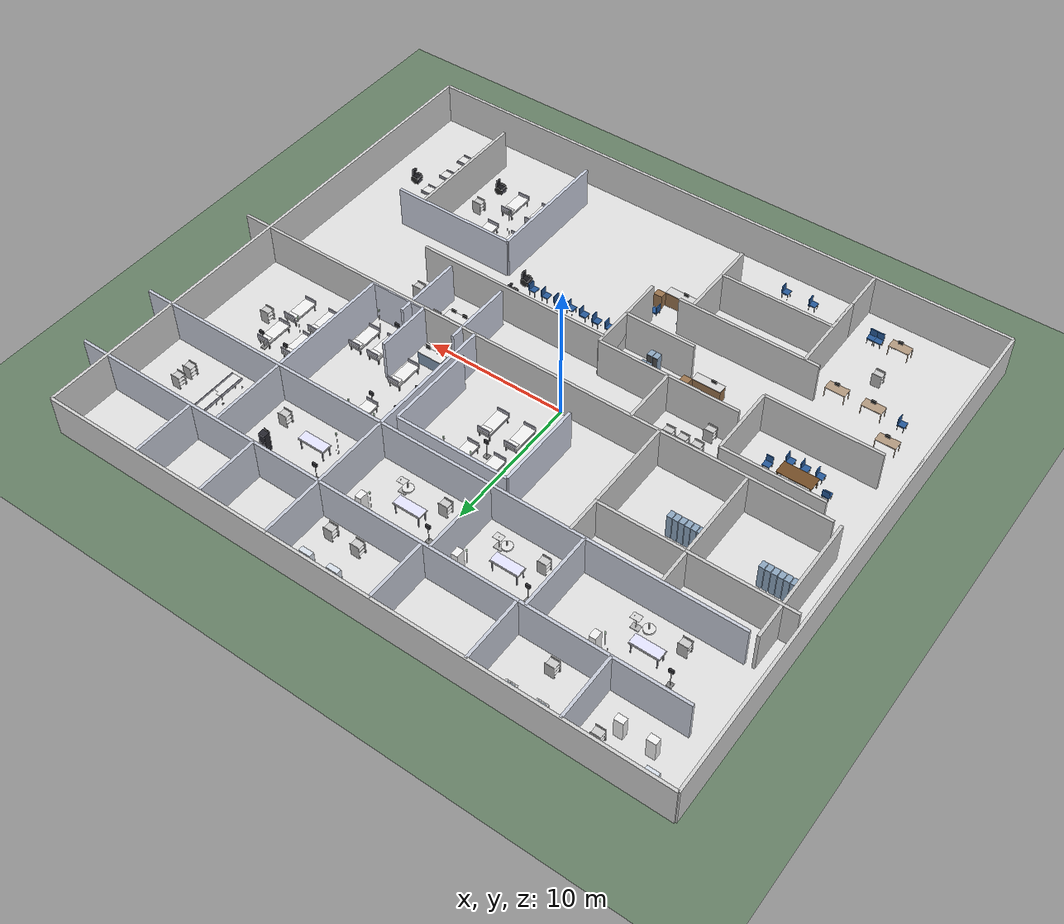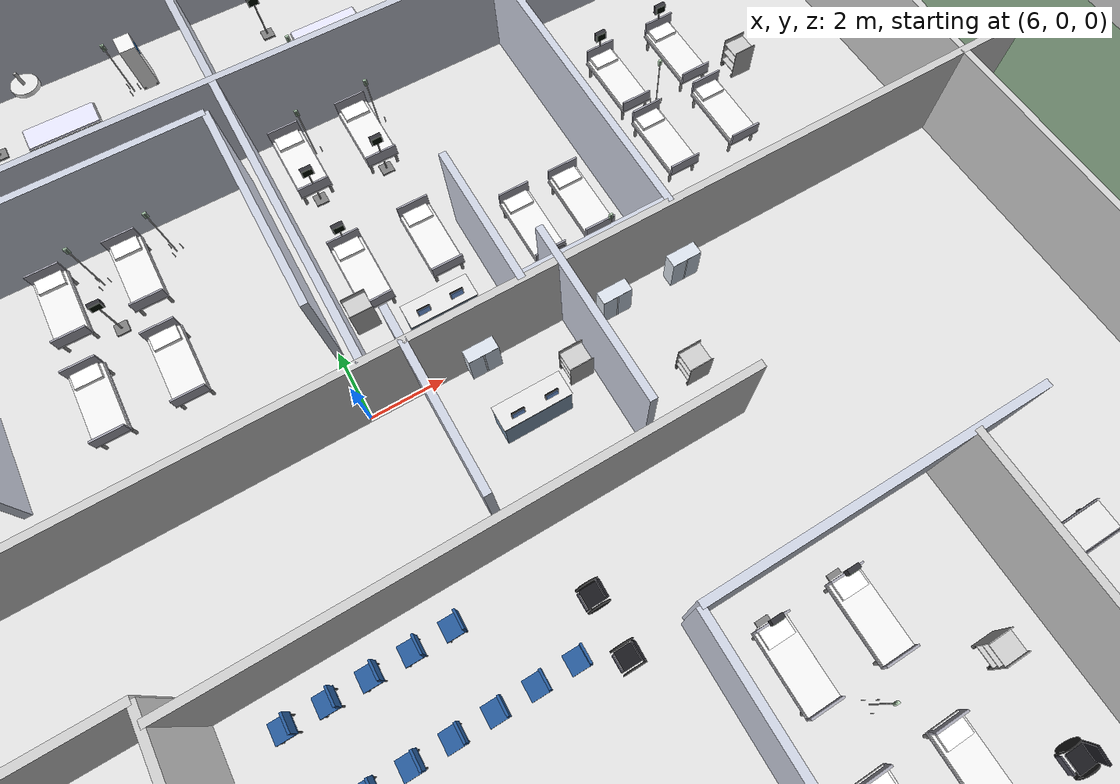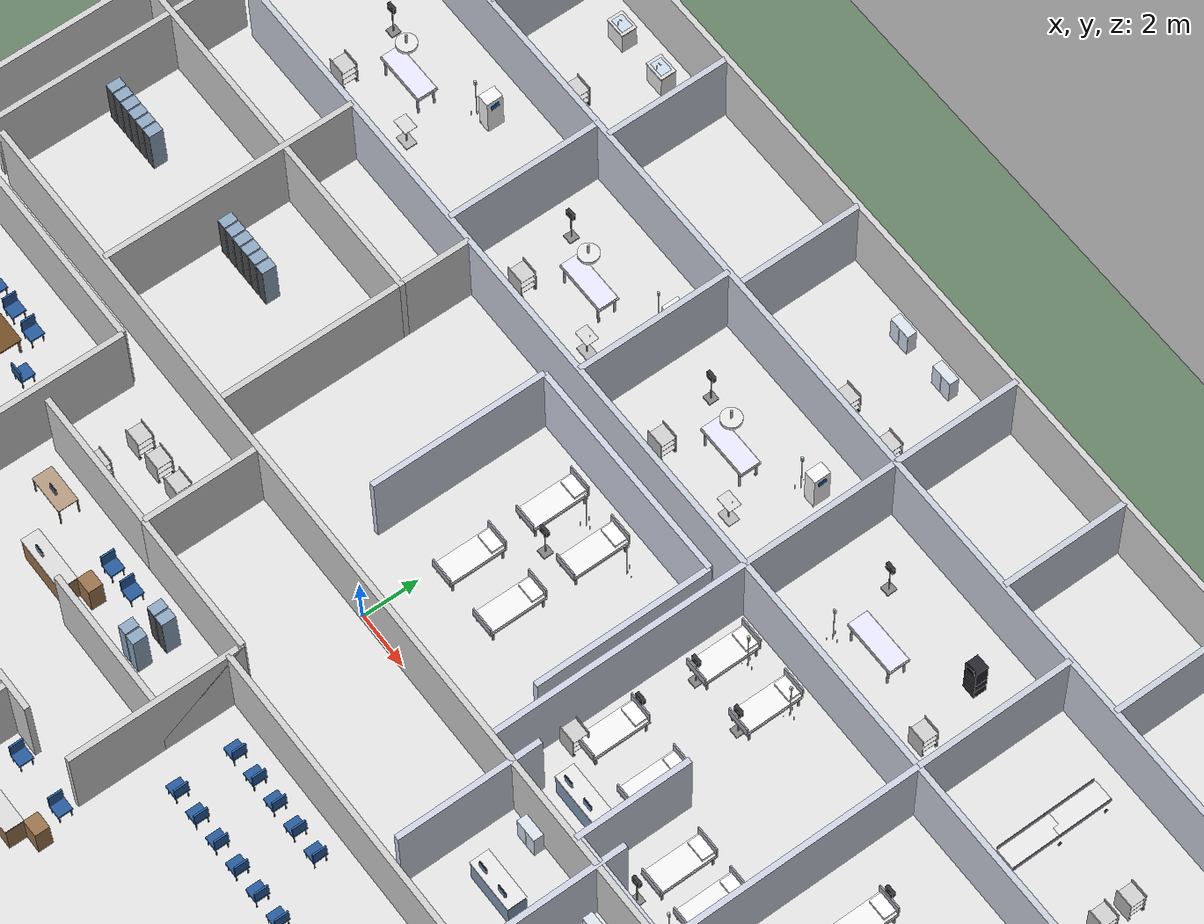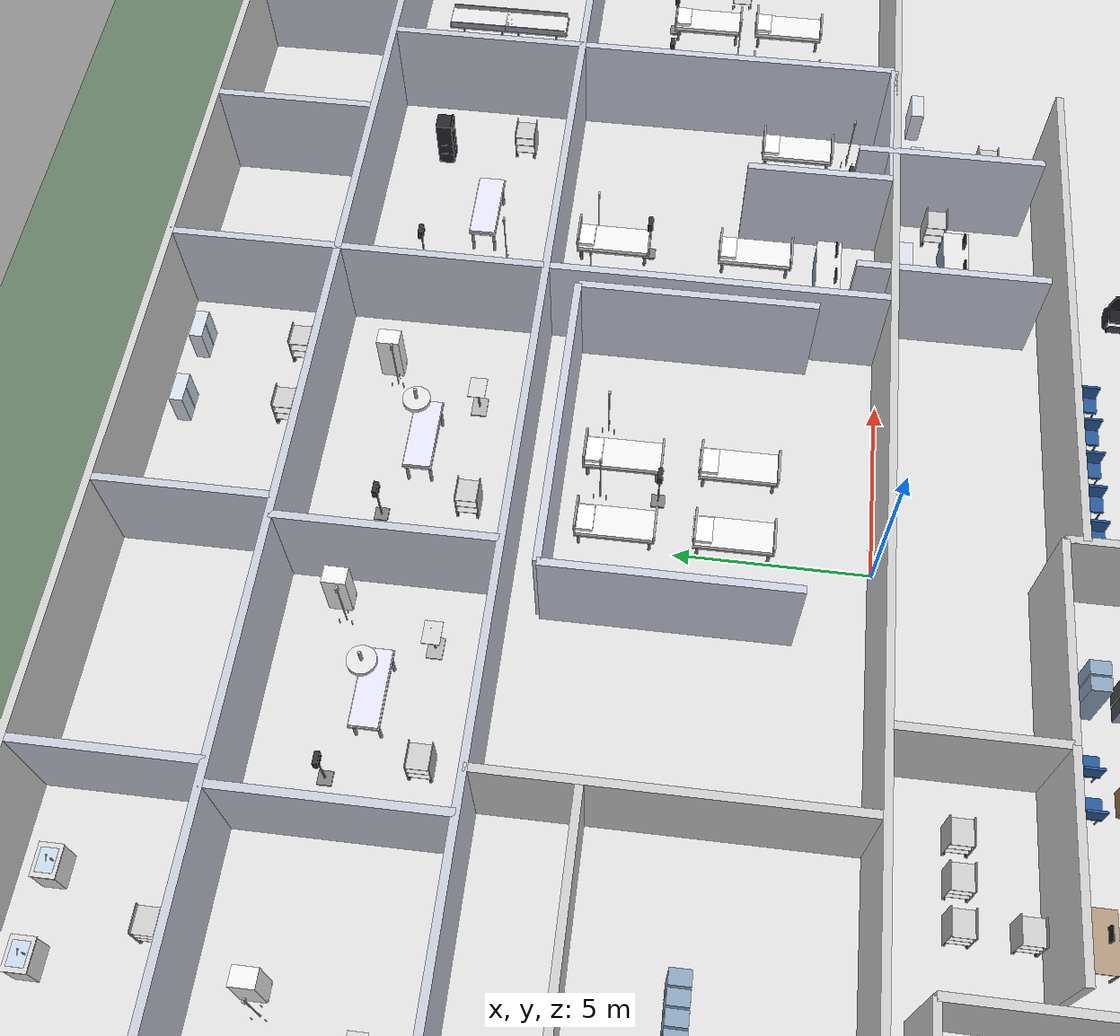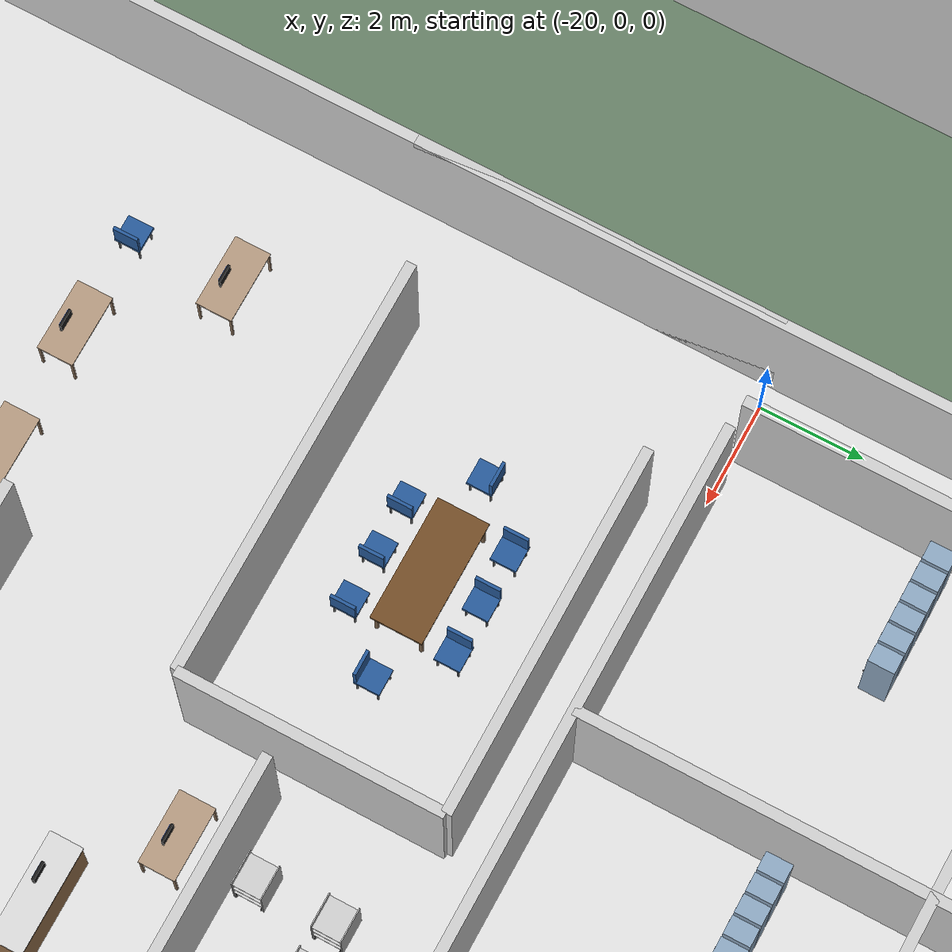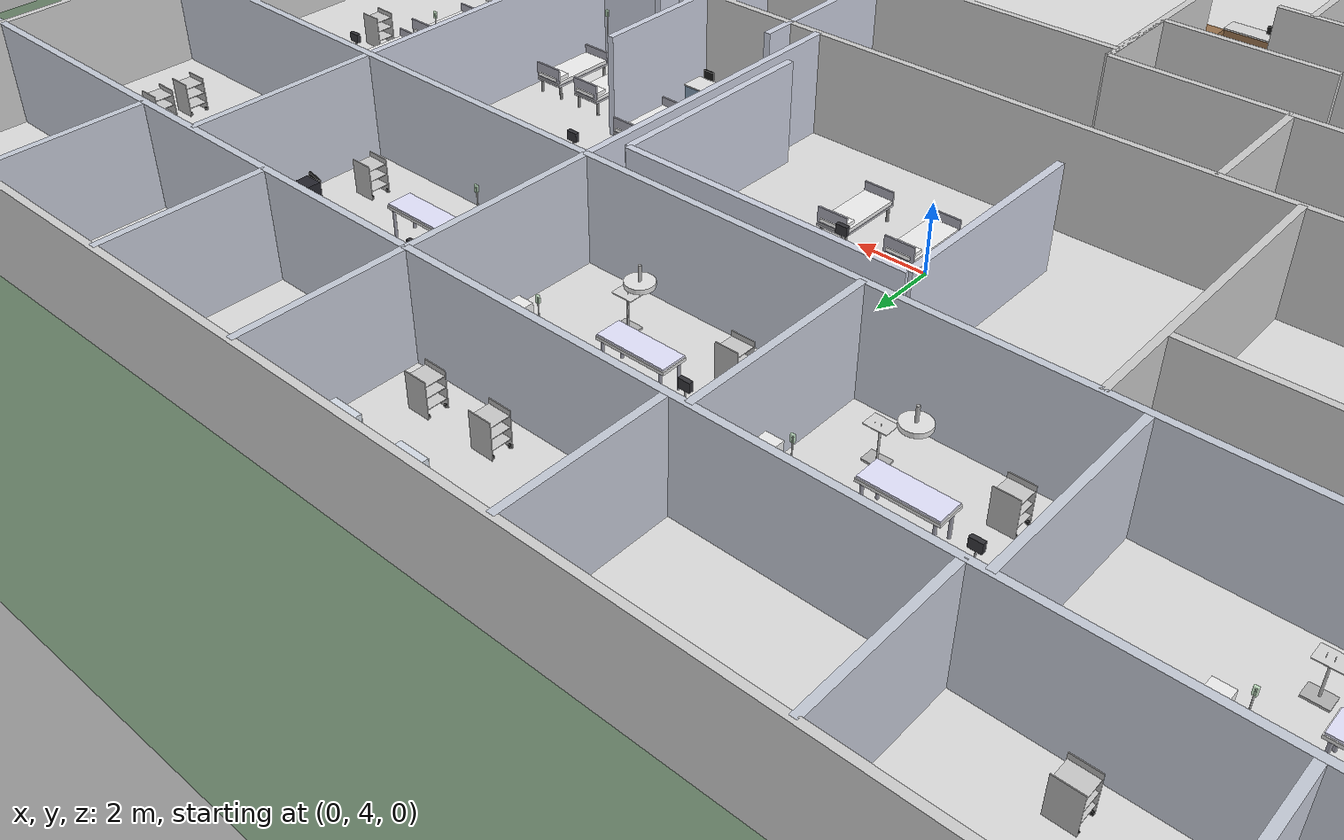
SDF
<?xml version="1.0"?>
<sdf version="1.6">
  <world name="hospital">

    <!-- ============================================================
         PHYSICS & ENVIRONMENT
         ============================================================ -->
    <physics type="ode">
      <real_time_update_rate>1000</real_time_update_rate>
      <max_step_size>0.001</max_step_size>
      <real_time_factor>1</real_time_factor>
    </physics>

    <gravity>0 0 -9.8</gravity>

    <!-- Ambient light - hospital fluorescent feel -->
    <scene>
      <ambient>0.6 0.6 0.65 1</ambient>
      <background>0.7 0.7 0.7 1</background>
      <shadows>true</shadows>
    </scene>

    <!-- Sun light -->
    <light name="sun" type="directional">
      <cast_shadows>false</cast_shadows>
      <pose>0 0 100 0 0 0</pose>
      <diffuse>0.7 0.7 0.7 1</diffuse>
      <specular>0.2 0.2 0.2 1</specular>
      <direction>0.1 0.1 -0.9</direction>
    </light>

    <!-- Overhead fluorescent lights per zone -->
    <light name="light_or_zone" type="point">
      <pose>-4.5 11.7 2.9 0 0 0</pose>
      <diffuse>0.9 0.9 0.95 1</diffuse><specular>0.3 0.3 0.3 1</specular>
      <attenuation><range>20</range><constant>0.4</constant><linear>0.05</linear><quadratic>0.001</quadratic></attenuation>
    </light>
    <light name="light_mid_zone" type="point">
      <pose>2.0 5.0 2.9 0 0 0</pose>
      <diffuse>0.85 0.85 0.9 1</diffuse><specular>0.2 0.2 0.2 1</specular>
      <attenuation><range>22</range><constant>0.4</constant><linear>0.05</linear><quadratic>0.001</quadratic></attenuation>
    </light>
    <light name="light_waiting" type="point">
      <pose>5.0 -8.0 2.9 0 0 0</pose>
      <diffuse>0.8 0.8 0.85 1</diffuse><specular>0.2 0.2 0.2 1</specular>
      <attenuation><range>20</range><constant>0.4</constant><linear>0.05</linear><quadratic>0.001</quadratic></attenuation>
    </light>
    <light name="light_admin" type="point">
      <pose>-7.0 -13.0 2.9 0 0 0</pose>
      <diffuse>0.8 0.8 0.85 1</diffuse><specular>0.2 0.2 0.2 1</specular>
      <attenuation><range>18</range><constant>0.4</constant><linear>0.05</linear><quadratic>0.001</quadratic></attenuation>
    </light>
    <light name="light_recovery" type="point">
      <pose>14.0 -10.0 2.9 0 0 0</pose>
      <diffuse>0.8 0.8 0.85 1</diffuse><specular>0.2 0.2 0.2 1</specular>
      <attenuation><range>14</range><constant>0.4</constant><linear>0.05</linear><quadratic>0.001</quadratic></attenuation>
    </light>

    <!-- ============================================================
         GROUND PLANE (outside building)
         ============================================================ -->
    <model name="ground_plane">
      <static>true</static>
      <link name="link">
        <collision name="collision">
          <geometry><plane><normal>0 0 1</normal><size>100 100</size></plane></geometry>
        </collision>
        <visual name="visual">
          <geometry><plane><normal>0 0 1</normal><size>100 100</size></plane></geometry>
          <material><ambient>0.4 0.5 0.4 1</ambient><diffuse>0.4 0.5 0.4 1</diffuse></material>
        </visual>
      </link>
    </model>

    <!-- ============================================================
         HOSPITAL BUILDING STRUCTURE
         ============================================================ -->
    <include>
      <uri>model://hospital_building</uri>
      <name>hospital_building</name>
      <pose>0 0 0 0 0 0</pose>
    </include>

    <include>
      <uri>model://operating_table</uri>
      <name>or1_table</name>
      <pose>-14.0 11.7 0 0 0 0</pose>
    </include>
    <include>
      <uri>model://anesthesia_machine</uri>
      <name>or1_anesthesia</name>
      <pose>-11.5 13.0 0 0 0 1.5708</pose>
    </include>
    <include>
      <uri>model://surgical_light</uri>
      <name>or1_light</name>
      <pose>-14.0 11.7 0 0 0 0</pose>
    </include>
    <include>
      <uri>model://instrument_table</uri>
      <name>or1_instruments</name>
      <pose>-12.5 10.5 0 0 0 0</pose>
    </include>
    <include>
      <uri>model://patient_monitor</uri>
      <name>or1_monitor</name>
      <pose>-16.0 12.5 0 0 0 0</pose>
    </include>
    <include>
      <uri>model://supply_cart</uri>
      <name>or1_supply</name>
      <pose>-15.5 10.3 0 0 0 0</pose>
    </include>
    <include>
      <uri>model://iv_stand</uri>
      <name>or1_iv</name>
      <pose>-12.0 12.8 0 0 0 0</pose>
    </include>

    <!-- ============================================================
         OPERATING ROOM 2  (x=-4.7, y=11.7)
         ============================================================ -->
    <include>
      <uri>model://operating_table</uri>
      <name>or2_table</name>
      <pose>-4.7 11.7 0 0 0 0</pose>
    </include>
    <include>
      <uri>model://anesthesia_machine</uri>
      <name>or2_anesthesia</name>
      <pose>-2.2 13.0 0 0 0 1.5708</pose>
    </include>
    <include>
      <uri>model://surgical_light</uri>
      <name>or2_light</name>
      <pose>-4.7 11.7 0 0 0 0</pose>
    </include>
    <include>
      <uri>model://instrument_table</uri>
      <name>or2_instruments</name>
      <pose>-3.2 10.5 0 0 0 0</pose>
    </include>
    <include>
      <uri>model://patient_monitor</uri>
      <name>or2_monitor</name>
      <pose>-6.7 12.5 0 0 0 0</pose>
    </include>
    <include>
      <uri>model://supply_cart</uri>
      <name>or2_supply</name>
      <pose>-6.2 10.3 0 0 0 0</pose>
    </include>
    <include>
      <uri>model://iv_stand</uri>
      <name>or2_iv</name>
      <pose>-2.7 12.8 0 0 0 0</pose>
    </include>

    <!-- ============================================================
         OPERATING ROOM 3  (x=2.3, y=11.7)
         ============================================================ -->
    <include>
      <uri>model://operating_table</uri>
      <name>or3_table</name>
      <pose>2.3 11.7 0 0 0 0</pose>
    </include>
    <include>
      <uri>model://anesthesia_machine</uri>
      <name>or3_anesthesia</name>
      <pose>4.8 13.0 0 0 0 1.5708</pose>
    </include>
    <include>
      <uri>model://surgical_light</uri>
      <name>or3_light</name>
      <pose>2.3 11.7 0 0 0 0</pose>
    </include>
    <include>
      <uri>model://instrument_table</uri>
      <name>or3_instruments</name>
      <pose>3.8 10.5 0 0 0 0</pose>
    </include>
    <include>
      <uri>model://patient_monitor</uri>
      <name>or3_monitor</name>
      <pose>0.3 12.5 0 0 0 0</pose>
    </include>
    <include>
      <uri>model://supply_cart</uri>
      <name>or3_supply</name>
      <pose>0.8 10.3 0 0 0 0</pose>
    </include>
    <include>
      <uri>model://iv_stand</uri>
      <name>or3_iv</name>
      <pose>4.3 12.8 0 0 0 0</pose>
    </include>

    <include>
      <uri>model://endoscopy_cart</uri>
      <name>endo_cart</name>
      <pose>12.5 12.8 0 0 0 0</pose>
    </include>
    <include>
      <uri>model://operating_table</uri>
      <name>endo_table</name>
      <pose>10.0 11.2 0 0 0 0</pose>
    </include>
    <include>
      <uri>model://patient_monitor</uri>
      <name>endo_monitor</name>
      <pose>8.5 12.8 0 0 0 0</pose>
    </include>
    <include>
      <uri>model://supply_cart</uri>
      <name>endo_supply</name>
      <pose>13.0 10.5 0 0 0 0</pose>
    </include>
    <include>
      <uri>model://iv_stand</uri>
      <name>endo_iv</name>
      <pose>8.8 10.5 0 0 0 0</pose>
    </include>

    <include>
      <uri>model://stretcher</uri>
      <name>equip_stretcher1</name>
      <pose>17.5 12.5 0 0 0 1.5708</pose>
    </include>
    <include>
      <uri>model://stretcher</uri>
      <name>equip_stretcher2</name>
      <pose>17.5 10.8 0 0 0 1.5708</pose>
    </include>
    <include>
      <uri>model://supply_cart</uri>
      <name>equip_supply1</name>
      <pose>20.5 12.0 0 0 0 0</pose>
    </include>
    <include>
      <uri>model://supply_cart</uri>
      <name>equip_supply2</name>
      <pose>20.5 11.0 0 0 0 0</pose>
    </include>

    <include>
      <uri>model://anesthesia_machine</uri>
      <name>anesth_wr_machine1</name>
      <pose>-17.5 16.5 0 0 0 0</pose>
    </include>
    <include>
      <uri>model://anesthesia_machine</uri>
      <name>anesth_wr_machine2</name>
      <pose>-15.5 16.5 0 0 0 0</pose>
    </include>
    <include>
      <uri>model://med_cabinet</uri>
      <name>anesth_med_cab</name>
      <pose>-18.5 18.2 0 0 0 0</pose>
    </include>
    <include>
      <uri>model://supply_cart</uri>
      <name>anesth_supply</name>
      <pose>-14.8 17.5 0 0 0 0</pose>
    </include>

    <include>
      <uri>model://decon_sink</uri>
      <name>decon_sink1</name>
      <pose>-11.5 18.0 0 0 0 0</pose>
    </include>
    <include>
      <uri>model://decon_sink</uri>
      <name>decon_sink2</name>
      <pose>-9.5 18.0 0 0 0 0</pose>
    </include>
    <include>
      <uri>model://supply_cart</uri>
      <name>decon_supply</name>
      <pose>-10.5 15.5 0 0 0 0</pose>
    </include>

    <include>
      <uri>model://med_cabinet</uri>
      <name>sterile_cab1</name>
      <pose>2.5 18.0 0 0 0 0</pose>
    </include>
    <include>
      <uri>model://med_cabinet</uri>
      <name>sterile_cab2</name>
      <pose>4.5 18.0 0 0 0 0</pose>
    </include>
    <include>
      <uri>model://supply_cart</uri>
      <name>sterile_supply1</name>
      <pose>3.0 15.5 0 0 0 0</pose>
    </include>
    <include>
      <uri>model://supply_cart</uri>
      <name>sterile_supply2</name>
      <pose>5.0 15.5 0 0 0 0</pose>
    </include>

    <include>
      <uri>model://locker</uri>
      <name>male_lock1</name>
      <pose>-18.5 4.0 0 0 0 0</pose>
    </include>
    <include>
      <uri>model://locker</uri>
      <name>male_lock2</name>
      <pose>-18.1 4.0 0 0 0 0</pose>
    </include>
    <include>
      <uri>model://locker</uri>
      <name>male_lock3</name>
      <pose>-17.7 4.0 0 0 0 0</pose>
    </include>
    <include>
      <uri>model://locker</uri>
      <name>male_lock4</name>
      <pose>-17.3 4.0 0 0 0 0</pose>
    </include>
    <include>
      <uri>model://locker</uri>
      <name>male_lock5</name>
      <pose>-16.9 4.0 0 0 0 0</pose>
    </include>
    <include>
      <uri>model://locker</uri>
      <name>male_lock6</name>
      <pose>-16.5 4.0 0 0 0 0</pose>
    </include>

    <!-- ============================================================
         FEMALE LOCKER ROOM  (x=-10, y=4.0)
         ============================================================ -->
    <include>
      <uri>model://locker</uri>
      <name>fem_lock1</name>
      <pose>-12.5 4.0 0 0 0 0</pose>
    </include>
    <include>
      <uri>model://locker</uri>
      <name>fem_lock2</name>
      <pose>-12.1 4.0 0 0 0 0</pose>
    </include>
    <include>
      <uri>model://locker</uri>
      <name>fem_lock3</name>
      <pose>-11.7 4.0 0 0 0 0</pose>
    </include>
    <include>
      <uri>model://locker</uri>
      <name>fem_lock4</name>
      <pose>-11.3 4.0 0 0 0 0</pose>
    </include>
    <include>
      <uri>model://locker</uri>
      <name>fem_lock5</name>
      <pose>-10.9 4.0 0 0 0 0</pose>
    </include>
    <include>
      <uri>model://locker</uri>
      <name>fem_lock6</name>
      <pose>-10.5 4.0 0 0 0 0</pose>
    </include>

    <include>
      <uri>model://hospital_bed</uri>
      <name>preop_bed1</name>
      <pose>0.5 6.5 0 0 0 1.5708</pose>
    </include>
    <include>
      <uri>model://hospital_bed</uri>
      <name>preop_bed2</name>
      <pose>2.5 6.5 0 0 0 1.5708</pose>
    </include>
    <include>
      <uri>model://hospital_bed</uri>
      <name>preop_bed3</name>
      <pose>0.5 3.5 0 0 0 1.5708</pose>
    </include>
    <include>
      <uri>model://hospital_bed</uri>
      <name>preop_bed4</name>
      <pose>2.5 3.5 0 0 0 1.5708</pose>
    </include>
    <include>
      <uri>model://iv_stand</uri>
      <name>preop_iv1</name>
      <pose>1.5 7.0 0 0 0 0</pose>
    </include>
    <include>
      <uri>model://iv_stand</uri>
      <name>preop_iv2</name>
      <pose>3.5 7.0 0 0 0 0</pose>
    </include>
    <include>
      <uri>model://patient_monitor</uri>
      <name>preop_mon1</name>
      <pose>1.5 5.5 0 0 0 0</pose>
    </include>

    <include>
      <uri>model://hospital_bed</uri>
      <name>pacu_bed1</name>
      <pose>7.5 7.5 0 0 0 1.5708</pose>
    </include>
    <include>
      <uri>model://hospital_bed</uri>
      <name>pacu_bed2</name>
      <pose>9.5 7.5 0 0 0 1.5708</pose>
    </include>
    <include>
      <uri>model://hospital_bed</uri>
      <name>pacu_bed3</name>
      <pose>7.5 3.5 0 0 0 1.5708</pose>
    </include>
    <include>
      <uri>model://hospital_bed</uri>
      <name>pacu_bed4</name>
      <pose>9.5 3.5 0 0 0 1.5708</pose>
    </include>
    <include>
      <uri>model://patient_monitor</uri>
      <name>pacu_mon1</name>
      <pose>7.5 6.5 0 0 0 0</pose>
    </include>
    <include>
      <uri>model://patient_monitor</uri>
      <name>pacu_mon2</name>
      <pose>9.5 6.5 0 0 0 0</pose>
    </include>
    <include>
      <uri>model://patient_monitor</uri>
      <name>pacu_mon3</name>
      <pose>7.5 4.5 0 0 0 0</pose>
    </include>
    <include>
      <uri>model://iv_stand</uri>
      <name>pacu_iv1</name>
      <pose>8.0 8.0 0 0 0 0</pose>
    </include>
    <include>
      <uri>model://iv_stand</uri>
      <name>pacu_iv2</name>
      <pose>10.0 8.0 0 0 0 0</pose>
    </include>
    <include>
      <uri>model://supply_cart</uri>
      <name>pacu_supply</name>
      <pose>7.0 2.5 0 0 0 0</pose>
    </include>
    <include>
      <uri>model://nurse_station</uri>
      <name>pacu_nurse_station</name>
      <pose>8.8 1.5 0 0 0 0</pose>
    </include>

    <!-- ============================================================
         PEDIATRIC / ISOLATION RECOVERY  (x=12.5, y=2.0)
         ============================================================ -->
    <include>
      <uri>model://hospital_bed</uri>
      <name>pedi_bed1</name>
      <pose>12.0 2.5 0 0 0 1.5708</pose>
    </include>
    <include>
      <uri>model://hospital_bed</uri>
      <name>pedi_bed2</name>
      <pose>13.5 2.5 0 0 0 1.5708</pose>
    </include>
    <include>
      <uri>model://patient_monitor</uri>
      <name>pedi_mon1</name>
      <pose>12.0 1.0 0 0 0 0</pose>
    </include>
    <include>
      <uri>model://iv_stand</uri>
      <name>pedi_iv1</name>
      <pose>13.5 1.0 0 0 0 0</pose>
    </include>

    <!-- ============================================================
         PRIMARY RECOVERY  (x=17, y=3)
         ============================================================ -->
    <include>
      <uri>model://hospital_bed</uri>
      <name>pri_rec_bed1</name>
      <pose>16.5 5.5 0 0 0 1.5708</pose>
    </include>
    <include>
      <uri>model://hospital_bed</uri>
      <name>pri_rec_bed2</name>
      <pose>18.5 5.5 0 0 0 1.5708</pose>
    </include>
    <include>
      <uri>model://hospital_bed</uri>
      <name>pri_rec_bed3</name>
      <pose>16.5 3.0 0 0 0 1.5708</pose>
    </include>
    <include>
      <uri>model://hospital_bed</uri>
      <name>pri_rec_bed4</name>
      <pose>18.5 3.0 0 0 0 1.5708</pose>
    </include>
    <include>
      <uri>model://patient_monitor</uri>
      <name>pri_rec_mon1</name>
      <pose>16.5 6.5 0 0 0 0</pose>
    </include>
    <include>
      <uri>model://patient_monitor</uri>
      <name>pri_rec_mon2</name>
      <pose>18.5 6.5 0 0 0 0</pose>
    </include>
    <include>
      <uri>model://iv_stand</uri>
      <name>pri_rec_iv1</name>
      <pose>17.2 4.5 0 0 0 0</pose>
    </include>
    <include>
      <uri>model://supply_cart</uri>
      <name>pri_rec_supply</name>
      <pose>20.0 4.5 0 0 0 0</pose>
    </include>

    <include>
      <uri>model://conference_table</uri>
      <name>conf_table</name>
      <pose>-14.5 -3.5 0 0 0 0</pose>
    </include>
    <include>
      <uri>model://waiting_chair</uri>
      <name>conf_chair1</name>
      <pose>-16.5 -3.5 0 0 0 1.5708</pose>
    </include>
    <include>
      <uri>model://waiting_chair</uri>
      <name>conf_chair2</name>
      <pose>-15.5 -2.5 0 0 0 3.14159</pose>
    </include>
    <include>
      <uri>model://waiting_chair</uri>
      <name>conf_chair3</name>
      <pose>-14.5 -2.5 0 0 0 3.14159</pose>
    </include>
    <include>
      <uri>model://waiting_chair</uri>
      <name>conf_chair4</name>
      <pose>-13.5 -2.5 0 0 0 3.14159</pose>
    </include>
    <include>
      <uri>model://waiting_chair</uri>
      <name>conf_chair5</name>
      <pose>-12.5 -3.5 0 0 0 -1.5708</pose>
    </include>
    <include>
      <uri>model://waiting_chair</uri>
      <name>conf_chair6</name>
      <pose>-15.5 -4.5 0 0 0 0</pose>
    </include>
    <include>
      <uri>model://waiting_chair</uri>
      <name>conf_chair7</name>
      <pose>-14.5 -4.5 0 0 0 0</pose>
    </include>
    <include>
      <uri>model://waiting_chair</uri>
      <name>conf_chair8</name>
      <pose>-13.5 -4.5 0 0 0 0</pose>
    </include>

    <include>
      <uri>model://supply_cart</uri>
      <name>bulk_cart1</name>
      <pose>-8.5 -2.0 0 0 0 0</pose>
    </include>
    <include>
      <uri>model://supply_cart</uri>
      <name>bulk_cart2</name>
      <pose>-7.5 -2.0 0 0 0 0</pose>
    </include>
    <include>
      <uri>model://supply_cart</uri>
      <name>bulk_cart3</name>
      <pose>-6.5 -2.0 0 0 0 0</pose>
    </include>
    <include>
      <uri>model://supply_cart</uri>
      <name>bulk_cart4</name>
      <pose>-8.5 -3.5 0 0 0 0</pose>
    </include>

    <include>
      <uri>model://locker</uri>
      <name>dress_lock1</name>
      <pose>-3.0 -5.0 0 0 0 0</pose>
    </include>
    <include>
      <uri>model://locker</uri>
      <name>dress_lock2</name>
      <pose>-2.6 -5.0 0 0 0 0</pose>
    </include>
    <include>
      <uri>model://locker</uri>
      <name>dress_lock3</name>
      <pose>-3.0 -6.0 0 0 0 3.14159</pose>
    </include>
    <include>
      <uri>model://locker</uri>
      <name>dress_lock4</name>
      <pose>-2.6 -6.0 0 0 0 3.14159</pose>
    </include>

    <include>
      <uri>model://reception_desk</uri>
      <name>admitting_desk</name>
      <pose>-6.5 -6.5 0 0 0 0</pose>
    </include>
    <include>
      <uri>model://office_desk</uri>
      <name>admitting_offdesk1</name>
      <pose>-8.5 -5.0 0 0 0 0</pose>
    </include>
    <include>
      <uri>model://waiting_chair</uri>
      <name>admitting_chair1</name>
      <pose>-5.5 -5.0 0 0 0 3.14159</pose>
    </include>
    <include>
      <uri>model://waiting_chair</uri>
      <name>admitting_chair2</name>
      <pose>-4.5 -5.0 0 0 0 3.14159</pose>
    </include>

    <include>
      <uri>model://waiting_chair</uri>
      <name>wait_chair1</name>
      <pose>1.5 -5.5 0 0 0 0</pose>
    </include>
    <include>
      <uri>model://waiting_chair</uri>
      <name>wait_chair2</name>
      <pose>2.5 -5.5 0 0 0 0</pose>
    </include>
    <include>
      <uri>model://waiting_chair</uri>
      <name>wait_chair3</name>
      <pose>3.5 -5.5 0 0 0 0</pose>
    </include>
    <include>
      <uri>model://waiting_chair</uri>
      <name>wait_chair4</name>
      <pose>4.5 -5.5 0 0 0 0</pose>
    </include>
    <include>
      <uri>model://waiting_chair</uri>
      <name>wait_chair5</name>
      <pose>5.5 -5.5 0 0 0 0</pose>
    </include>
    <include>
      <uri>model://waiting_chair</uri>
      <name>wait_chair6</name>
      <pose>1.5 -7.5 0 0 0 0</pose>
    </include>
    <include>
      <uri>model://waiting_chair</uri>
      <name>wait_chair7</name>
      <pose>2.5 -7.5 0 0 0 0</pose>
    </include>
    <include>
      <uri>model://waiting_chair</uri>
      <name>wait_chair8</name>
      <pose>3.5 -7.5 0 0 0 0</pose>
    </include>
    <include>
      <uri>model://waiting_chair</uri>
      <name>wait_chair9</name>
      <pose>4.5 -7.5 0 0 0 0</pose>
    </include>
    <include>
      <uri>model://waiting_chair</uri>
      <name>wait_chair10</name>
      <pose>5.5 -7.5 0 0 0 0</pose>
    </include>
    <include>
      <uri>model://waiting_chair</uri>
      <name>wait_chair11</name>
      <pose>6.5 -7.5 0 0 0 0</pose>
    </include>
    <include>
      <uri>model://waiting_chair</uri>
      <name>wait_chair12</name>
      <pose>7.5 -7.5 0 0 0 0</pose>
    </include>
    <include>
      <uri>model://wheelchair</uri>
      <name>waiting_wheelchair1</name>
      <pose>8.5 -6.5 0 0 0 0</pose>
    </include>
    <include>
      <uri>model://wheelchair</uri>
      <name>waiting_wheelchair2</name>
      <pose>8.5 -8.0 0 0 0 0</pose>
    </include>

    <!-- ============================================================
         NURSE STATION  (x=9.5, y=-2.0)
         ============================================================ -->
    <include>
      <uri>model://nurse_station</uri>
      <name>main_nurse_station</name>
      <pose>9.5 -2.0 0 0 0 0</pose>
    </include>
    <include>
      <uri>model://med_cabinet</uri>
      <name>nurse_med_cab</name>
      <pose>9.0 -0.5 0 0 0 0</pose>
    </include>
    <include>
      <uri>model://supply_cart</uri>
      <name>nurse_supply</name>
      <pose>11.0 -1.5 0 0 0 0</pose>
    </include>

    <!-- ============================================================
         MED PREP  (x=13.5, y=-2.0)
         ============================================================ -->
    <include>
      <uri>model://med_cabinet</uri>
      <name>medprep_cab1</name>
      <pose>12.5 -0.8 0 0 0 0</pose>
    </include>
    <include>
      <uri>model://med_cabinet</uri>
      <name>medprep_cab2</name>
      <pose>14.5 -0.8 0 0 0 0</pose>
    </include>
    <include>
      <uri>model://supply_cart</uri>
      <name>medprep_supply</name>
      <pose>13.5 -3.0 0 0 0 0</pose>
    </include>

    <include>
      <uri>model://hospital_bed</uri>
      <name>sec_rec_bed1</name>
      <pose>11.5 -10.0 0 0 0 1.5708</pose>
    </include>
    <include>
      <uri>model://hospital_bed</uri>
      <name>sec_rec_bed2</name>
      <pose>13.5 -10.0 0 0 0 1.5708</pose>
    </include>
    <include>
      <uri>model://hospital_bed</uri>
      <name>sec_rec_bed3</name>
      <pose>11.5 -13.5 0 0 0 1.5708</pose>
    </include>
    <include>
      <uri>model://hospital_bed</uri>
      <name>sec_rec_bed4</name>
      <pose>13.5 -13.5 0 0 0 1.5708</pose>
    </include>
    <include>
      <uri>model://patient_monitor</uri>
      <name>sec_rec_mon1</name>
      <pose>11.5 -9.0 0 0 0 0</pose>
    </include>
    <include>
      <uri>model://patient_monitor</uri>
      <name>sec_rec_mon2</name>
      <pose>13.5 -9.0 0 0 0 0</pose>
    </include>
    <include>
      <uri>model://iv_stand</uri>
      <name>sec_rec_iv1</name>
      <pose>12.5 -11.5 0 0 0 0</pose>
    </include>
    <include>
      <uri>model://supply_cart</uri>
      <name>sec_rec_supply</name>
      <pose>15.5 -12.0 0 0 0 0</pose>
    </include>
    <include>
      <uri>model://wheelchair</uri>
      <name>sec_rec_wheelchair</name>
      <pose>15.5 -14.5 0 0 0 0</pose>
    </include>

    <!-- ============================================================
         STRETCHER STORAGE  (x=20, y=-13.0)
         ============================================================ -->
    <include>
      <uri>model://stretcher</uri>
      <name>stretch_storage1</name>
      <pose>18.5 -11.0 0 0 0 0</pose>
    </include>
    <include>
      <uri>model://stretcher</uri>
      <name>stretch_storage2</name>
      <pose>18.5 -13.0 0 0 0 0</pose>
    </include>
    <include>
      <uri>model://stretcher</uri>
      <name>stretch_storage3</name>
      <pose>18.5 -15.0 0 0 0 0</pose>
    </include>
    <include>
      <uri>model://wheelchair</uri>
      <name>stretch_wheelchair</name>
      <pose>21.0 -12.0 0 0 0 0</pose>
    </include>

    <include>
      <uri>model://reception_desk</uri>
      <name>reception_desk_main</name>
      <pose>-1.0 -12.0 0 0 0 0</pose>
    </include>
    <include>
      <uri>model://waiting_chair</uri>
      <name>recep_chair1</name>
      <pose>0.0 -10.5 0 0 0 3.14159</pose>
    </include>
    <include>
      <uri>model://waiting_chair</uri>
      <name>recep_chair2</name>
      <pose>-2.0 -10.5 0 0 0 3.14159</pose>
    </include>
    <include>
      <uri>model://wheelchair</uri>
      <name>recep_wheelchair</name>
      <pose>-3.5 -11.0 0 0 0 0</pose>
    </include>

    <include>
      <uri>model://office_desk</uri>
      <name>records_desk1</name>
      <pose>-13.0 -11.0 0 0 0 0</pose>
    </include>
    <include>
      <uri>model://office_desk</uri>
      <name>records_desk2</name>
      <pose>-15.5 -11.0 0 0 0 0</pose>
    </include>
    <include>
      <uri>model://supply_cart</uri>
      <name>records_cart</name>
      <pose>-14.5 -13.5 0 0 0 0</pose>
    </include>

    <include>
      <uri>model://office_desk</uri>
      <name>biz_desk1</name>
      <pose>-8.0 -15.0 0 0 0 0</pose>
    </include>
    <include>
      <uri>model://office_desk</uri>
      <name>biz_desk2</name>
      <pose>-6.0 -15.0 0 0 0 0</pose>
    </include>
    <include>
      <uri>model://office_desk</uri>
      <name>biz_desk3</name>
      <pose>-4.5 -15.0 0 0 0 0</pose>
    </include>
    <include>
      <uri>model://waiting_chair</uri>
      <name>biz_chair1</name>
      <pose>-8.0 -17.0 0 0 0 0</pose>
    </include>
    <include>
      <uri>model://waiting_chair</uri>
      <name>biz_chair2</name>
      <pose>-6.0 -17.0 0 0 0 0</pose>
    </include>

    <include>
      <uri>model://office_desk</uri>
      <name>dir_nurses_desk</name>
      <pose>-14.5 -16.5 0 0 0 0</pose>
    </include>
    <include>
      <uri>model://waiting_chair</uri>
      <name>dir_chair1</name>
      <pose>-13.0 -16.5 0 0 0 -1.5708</pose>
    </include>
    <include>
      <uri>model://waiting_chair</uri>
      <name>dir_chair2</name>
      <pose>-12.5 -16.5 0 0 0 -1.5708</pose>
    </include>

    <include>
      <uri>model://office_desk</uri>
      <name>staff_office_desk</name>
      <pose>-17.5 -9.0 0 0 0 0</pose>
    </include>
    <include>
      <uri>model://waiting_chair</uri>
      <name>staff_chair1</name>
      <pose>-17.5 -11.0 0 0 0 0</pose>
    </include>

  </world>
</sdf>

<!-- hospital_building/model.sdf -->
<sdf version="1.6">
  <model name="hospital_building">
    <static>true</static>

    <link name="floor">
      <pose>1.5 0 -0.05 0 0 0</pose>
      <collision name="c"><geometry><box><size>44 38 0.1</size></box></geometry></collision>
      <visual name="v">
        <geometry><box><size>44 38 0.1</size></box></geometry>
        <material>
          <ambient>0.88 0.88 0.88 1</ambient>
          <diffuse>0.88 0.88 0.88 1</diffuse>
        </material>
      </visual>
    </link>

    <!-- ================================================================
         OUTER PERIMETER WALLS  (thickness=0.2, height=3.0)
         ================================================================ -->
    <!-- North wall -->
    <link name="wall_north">
      <pose>1.5 19.0 1.5 0 0 0</pose>
      <collision name="c"><geometry><box><size>44 0.2 3.0</size></box></geometry></collision>
      <visual name="v"><geometry><box><size>44 0.2 3.0</size></box></geometry>
        <material><ambient>0.82 0.82 0.82 1</ambient><diffuse>0.82 0.82 0.82 1</diffuse></material></visual>
    </link>
    <!-- South wall -->
    <link name="wall_south">
      <pose>1.5 -19.0 1.5 0 0 0</pose>
      <collision name="c"><geometry><box><size>44 0.2 3.0</size></box></geometry></collision>
      <visual name="v"><geometry><box><size>44 0.2 3.0</size></box></geometry>
        <material><ambient>0.82 0.82 0.82 1</ambient><diffuse>0.82 0.82 0.82 1</diffuse></material></visual>
    </link>
    <!-- East wall -->
    <link name="wall_east">
      <pose>23.5 0 1.5 0 0 0</pose>
      <collision name="c"><geometry><box><size>0.2 38 3.0</size></box></geometry></collision>
      <visual name="v"><geometry><box><size>0.2 38 3.0</size></box></geometry>
        <material><ambient>0.82 0.82 0.82 1</ambient><diffuse>0.82 0.82 0.82 1</diffuse></material></visual>
    </link>
    <!-- West wall -->
    <link name="wall_west">
      <pose>-20.5 0 1.5 0 0 0</pose>
      <collision name="c"><geometry><box><size>0.2 38 3.0</size></box></geometry></collision>
      <visual name="v"><geometry><box><size>0.2 38 3.0</size></box></geometry>
        <material><ambient>0.82 0.82 0.82 1</ambient><diffuse>0.82 0.82 0.82 1</diffuse></material></visual>
    </link>

    <!-- Clean core south wall (corridor between OR zone and mid zone) -->
    <link name="wall_clean_core_south">
      <pose>3.5 9.0 1.5 0 0 0</pose>
      <collision name="c"><geometry><box><size>44 0.2 3.0</size></box></geometry></collision>
      <visual name="v"><geometry><box><size>44 0.2 3.0</size></box></geometry>
        <material><ambient>0.78 0.80 0.85 1</ambient><diffuse>0.78 0.80 0.85 1</diffuse></material></visual>
    </link>

    <!-- Internal wall separating prep/clean core from OR corridor (y=14.5) -->
    <link name="wall_clean_core_internal">
      <pose>3.5 14.5 1.5 0 0 0</pose>
      <collision name="c"><geometry><box><size>44 0.2 3.0</size></box></geometry></collision>
      <visual name="v"><geometry><box><size>44 0.2 3.0</size></box></geometry>
        <material><ambient>0.78 0.80 0.85 1</ambient><diffuse>0.78 0.80 0.85 1</diffuse></material></visual>
    </link>

    <!-- Vertical partitions between OR rooms (x-separators in OR zone) -->
    <!-- Between OR1 and OR2 -->
    <link name="or_sep_1_2">
      <pose>-8.0 11.75 1.5 0 0 0</pose>
      <collision name="c"><geometry><box><size>0.2 5.5 3.0</size></box></geometry></collision>
      <visual name="v"><geometry><box><size>0.2 5.5 3.0</size></box></geometry>
        <material><ambient>0.78 0.80 0.85 1</ambient><diffuse>0.78 0.80 0.85 1</diffuse></material></visual>
    </link>
    <!-- Between OR2 and OR3 -->
    <link name="or_sep_2_3">
      <pose>-1.5 11.75 1.5 0 0 0</pose>
      <collision name="c"><geometry><box><size>0.2 5.5 3.0</size></box></geometry></collision>
      <visual name="v"><geometry><box><size>0.2 5.5 3.0</size></box></geometry>
        <material><ambient>0.78 0.80 0.85 1</ambient><diffuse>0.78 0.80 0.85 1</diffuse></material></visual>
    </link>
    <!-- Between OR3 and Endoscopy -->
    <link name="or_sep_3_endo">
      <pose>6.5 11.75 1.5 0 0 0</pose>
      <collision name="c"><geometry><box><size>0.2 5.5 3.0</size></box></geometry></collision>
      <visual name="v"><geometry><box><size>0.2 5.5 3.0</size></box></geometry>
        <material><ambient>0.78 0.80 0.85 1</ambient><diffuse>0.78 0.80 0.85 1</diffuse></material></visual>
    </link>
    <!-- Equipment storage east separator -->
    <link name="or_equip_sep">
      <pose>14.5 11.75 1.5 0 0 0</pose>
      <collision name="c"><geometry><box><size>0.2 5.5 3.0</size></box></geometry></collision>
      <visual name="v"><geometry><box><size>0.2 5.5 3.0</size></box></geometry>
        <material><ambient>0.78 0.80 0.85 1</ambient><diffuse>0.78 0.80 0.85 1</diffuse></material></visual>
    </link>

    <!-- Clean core north block internal separators (prep/pack, sterilize, storage) -->
    <link name="clean_sep1"><pose>-13.5 16.75 1.5 0 0 0</pose>
      <collision name="c"><geometry><box><size>0.2 4.5 3.0</size></box></geometry></collision>
      <visual name="v"><geometry><box><size>0.2 4.5 3.0</size></box></geometry>
        <material><ambient>0.78 0.80 0.85 1</ambient><diffuse>0.78 0.80 0.85 1</diffuse></material></visual>
    </link>
    <link name="clean_sep2"><pose>-7.5 16.75 1.5 0 0 0</pose>
      <collision name="c"><geometry><box><size>0.2 4.5 3.0</size></box></geometry></collision>
      <visual name="v"><geometry><box><size>0.2 4.5 3.0</size></box></geometry>
        <material><ambient>0.78 0.80 0.85 1</ambient><diffuse>0.78 0.80 0.85 1</diffuse></material></visual>
    </link>
    <link name="clean_sep3"><pose>-1.0 16.75 1.5 0 0 0</pose>
      <collision name="c"><geometry><box><size>0.2 4.5 3.0</size></box></geometry></collision>
      <visual name="v"><geometry><box><size>0.2 4.5 3.0</size></box></geometry>
        <material><ambient>0.78 0.80 0.85 1</ambient><diffuse>0.78 0.80 0.85 1</diffuse></material></visual>
    </link>
    <link name="clean_sep4"><pose>6.5 16.75 1.5 0 0 0</pose>
      <collision name="c"><geometry><box><size>0.2 4.5 3.0</size></box></geometry></collision>
      <visual name="v"><geometry><box><size>0.2 4.5 3.0</size></box></geometry>
        <material><ambient>0.78 0.80 0.85 1</ambient><diffuse>0.78 0.80 0.85 1</diffuse></material></visual>
    </link>
    <link name="clean_sep5"><pose>11.5 16.75 1.5 0 0 0</pose>
      <collision name="c"><geometry><box><size>0.2 4.5 3.0</size></box></geometry></collision>
      <visual name="v"><geometry><box><size>0.2 4.5 3.0</size></box></geometry>
        <material><ambient>0.78 0.80 0.85 1</ambient><diffuse>0.78 0.80 0.85 1</diffuse></material></visual>
    </link>
    <link name="clean_sep6"><pose>16.5 16.75 1.5 0 0 0</pose>
      <collision name="c"><geometry><box><size>0.2 4.5 3.0</size></box></geometry></collision>
      <visual name="v"><geometry><box><size>0.2 4.5 3.0</size></box></geometry>
        <material><ambient>0.78 0.80 0.85 1</ambient><diffuse>0.78 0.80 0.85 1</diffuse></material></visual>
    </link>

    <!-- Mid zone south wall (between mid and admin/waiting) -->
    <link name="wall_mid_south">
      <pose>3.5 0.0 1.5 0 0 0</pose>
      <collision name="c"><geometry><box><size>44 0.2 3.0</size></box></geometry></collision>
      <visual name="v"><geometry><box><size>44 0.2 3.0</size></box></geometry>
        <material><ambient>0.80 0.80 0.80 1</ambient><diffuse>0.80 0.80 0.80 1</diffuse></material></visual>
    </link>

    <!-- Locker/toilet separators west portion (x=-20.5 to x=-5) -->
    <link name="lock_sep1"><pose>-19.0 4.5 1.5 0 0 0</pose>
      <collision name="c"><geometry><box><size>0.2 9.0 3.0</size></box></geometry></collision>
      <visual name="v"><geometry><box><size>0.2 9.0 3.0</size></box></geometry>
        <material><ambient>0.80 0.80 0.80 1</ambient><diffuse>0.80 0.80 0.80 1</diffuse></material></visual>
    </link>
    <link name="lock_sep2"><pose>-13.0 4.5 1.5 0 0 0</pose>
      <collision name="c"><geometry><box><size>0.2 9.0 3.0</size></box></geometry></collision>
      <visual name="v"><geometry><box><size>0.2 9.0 3.0</size></box></geometry>
        <material><ambient>0.80 0.80 0.80 1</ambient><diffuse>0.80 0.80 0.80 1</diffuse></material></visual>
    </link>
    <link name="lock_sep3"><pose>-7.0 4.5 1.5 0 0 0</pose>
      <collision name="c"><geometry><box><size>0.2 9.0 3.0</size></box></geometry></collision>
      <visual name="v"><geometry><box><size>0.2 9.0 3.0</size></box></geometry>
        <material><ambient>0.80 0.80 0.80 1</ambient><diffuse>0.80 0.80 0.80 1</diffuse></material></visual>
    </link>
    <!-- Mid-zone horizontal separator (toilet row) -->
    <link name="lock_horiz"><pose>-13.5 6.5 1.5 0 0 0</pose>
      <collision name="c"><geometry><box><size>13.2 0.2 3.0</size></box></geometry></collision>
      <visual name="v"><geometry><box><size>13.2 0.2 3.0</size></box></geometry>
        <material><ambient>0.80 0.80 0.80 1</ambient><diffuse>0.80 0.80 0.80 1</diffuse></material></visual>
    </link>

    <!-- Pre-op Holding box (center approx x=2, y=5, size 8x6) -->
    <link name="preop_north"><pose>2.0 8.1 1.5 0 0 0</pose>
      <collision name="c"><geometry><box><size>8.0 0.2 3.0</size></box></geometry></collision>
      <visual name="v"><geometry><box><size>8.0 0.2 3.0</size></box></geometry>
        <material><ambient>0.80 0.82 0.88 1</ambient><diffuse>0.80 0.82 0.88 1</diffuse></material></visual>
    </link>
    <link name="preop_west"><pose>-2.0 5.0 1.5 0 0 0</pose>
      <collision name="c"><geometry><box><size>0.2 6.2 3.0</size></box></geometry></collision>
      <visual name="v"><geometry><box><size>0.2 6.2 3.0</size></box></geometry>
        <material><ambient>0.80 0.82 0.88 1</ambient><diffuse>0.80 0.82 0.88 1</diffuse></material></visual>
    </link>
    <link name="preop_east"><pose>6.0 5.0 1.5 0 0 0</pose>
      <collision name="c"><geometry><box><size>0.2 6.2 3.0</size></box></geometry></collision>
      <visual name="v"><geometry><box><size>0.2 6.2 3.0</size></box></geometry>
        <material><ambient>0.80 0.82 0.88 1</ambient><diffuse>0.80 0.82 0.88 1</diffuse></material></visual>
    </link>

    <!-- PACU zone east walls -->
    <link name="pacu_west"><pose>6.5 4.5 1.5 0 0 0</pose>
      <collision name="c"><geometry><box><size>0.2 9.0 3.0</size></box></geometry></collision>
      <visual name="v"><geometry><box><size>0.2 9.0 3.0</size></box></geometry>
        <material><ambient>0.80 0.82 0.88 1</ambient><diffuse>0.80 0.82 0.88 1</diffuse></material></visual>
    </link>
    <!-- Primary recovery east partition -->
    <link name="primary_rec_sep"><pose>14.5 4.5 1.5 0 0 0</pose>
      <collision name="c"><geometry><box><size>0.2 9.0 3.0</size></box></geometry></collision>
      <visual name="v"><geometry><box><size>0.2 9.0 3.0</size></box></geometry>
        <material><ambient>0.80 0.82 0.88 1</ambient><diffuse>0.80 0.82 0.88 1</diffuse></material></visual>
    </link>
    <!-- Pediatric/isolation separator -->
    <link name="pedi_sep"><pose>10.5 2.0 1.5 0 0 0</pose>
      <collision name="c"><geometry><box><size>0.2 4.0 3.0</size></box></geometry></collision>
      <visual name="v"><geometry><box><size>0.2 4.0 3.0</size></box></geometry>
        <material><ambient>0.80 0.82 0.88 1</ambient><diffuse>0.80 0.82 0.88 1</diffuse></material></visual>
    </link>
    <link name="pedi_horiz"><pose>12.5 0.1 1.5 0 0 0</pose>
      <collision name="c"><geometry><box><size>4.0 0.2 3.0</size></box></geometry></collision>
      <visual name="v"><geometry><box><size>4.0 0.2 3.0</size></box></geometry>
        <material><ambient>0.80 0.82 0.88 1</ambient><diffuse>0.80 0.82 0.88 1</diffuse></material></visual>
    </link>

    <!-- Conference room box -->
    <link name="conf_north"><pose>-14.0 -1.0 1.5 0 0 0</pose>
      <collision name="c"><geometry><box><size>7.0 0.2 3.0</size></box></geometry></collision>
      <visual name="v"><geometry><box><size>7.0 0.2 3.0</size></box></geometry>
        <material><ambient>0.80 0.80 0.80 1</ambient><diffuse>0.80 0.80 0.80 1</diffuse></material></visual>
    </link>
    <link name="conf_east"><pose>-10.5 -3.5 1.5 0 0 0</pose>
      <collision name="c"><geometry><box><size>0.2 5.0 3.0</size></box></geometry></collision>
      <visual name="v"><geometry><box><size>0.2 5.0 3.0</size></box></geometry>
        <material><ambient>0.80 0.80 0.80 1</ambient><diffuse>0.80 0.80 0.80 1</diffuse></material></visual>
    </link>
    <link name="conf_south"><pose>-14.5 -6.0 1.5 0 0 0</pose>
      <collision name="c"><geometry><box><size>8.0 0.2 3.0</size></box></geometry></collision>
      <visual name="v"><geometry><box><size>8.0 0.2 3.0</size></box></geometry>
        <material><ambient>0.80 0.80 0.80 1</ambient><diffuse>0.80 0.80 0.80 1</diffuse></material></visual>
    </link>

    <!-- Bulk storage partition -->
    <link name="bulk_sep"><pose>-5.0 -2.0 1.5 0 0 0</pose>
      <collision name="c"><geometry><box><size>0.2 4.0 3.0</size></box></geometry></collision>
      <visual name="v"><geometry><box><size>0.2 4.0 3.0</size></box></geometry>
        <material><ambient>0.80 0.80 0.80 1</ambient><diffuse>0.80 0.80 0.80 1</diffuse></material></visual>
    </link>
    <link name="bulk_south"><pose>-7.5 -4.0 1.5 0 0 0</pose>
      <collision name="c"><geometry><box><size>5.0 0.2 3.0</size></box></geometry></collision>
      <visual name="v"><geometry><box><size>5.0 0.2 3.0</size></box></geometry>
        <material><ambient>0.80 0.80 0.80 1</ambient><diffuse>0.80 0.80 0.80 1</diffuse></material></visual>
    </link>

    <!-- Dressing rooms partition -->
    <link name="dress_north"><pose>-2.5 -4.0 1.5 0 0 0</pose>
      <collision name="c"><geometry><box><size>5.0 0.2 3.0</size></box></geometry></collision>
      <visual name="v"><geometry><box><size>5.0 0.2 3.0</size></box></geometry>
        <material><ambient>0.80 0.80 0.80 1</ambient><diffuse>0.80 0.80 0.80 1</diffuse></material></visual>
    </link>
    <link name="dress_east"><pose>0.0 -5.5 1.5 0 0 0</pose>
      <collision name="c"><geometry><box><size>0.2 3.0 3.0</size></box></geometry></collision>
      <visual name="v"><geometry><box><size>0.2 3.0 3.0</size></box></geometry>
        <material><ambient>0.80 0.80 0.80 1</ambient><diffuse>0.80 0.80 0.80 1</diffuse></material></visual>
    </link>
    <link name="dress_south"><pose>-2.5 -7.0 1.5 0 0 0</pose>
      <collision name="c"><geometry><box><size>5.0 0.2 3.0</size></box></geometry></collision>
      <visual name="v"><geometry><box><size>5.0 0.2 3.0</size></box></geometry>
        <material><ambient>0.80 0.80 0.80 1</ambient><diffuse>0.80 0.80 0.80 1</diffuse></material></visual>
    </link>

    <!-- Admitting / Waiting divider -->
    <link name="admit_waiting_sep"><pose>0.0 -7.0 1.5 0 0 0</pose>
      <collision name="c"><geometry><box><size>0.2 6.0 3.0</size></box></geometry></collision>
      <visual name="v"><geometry><box><size>0.2 6.0 3.0</size></box></geometry>
        <material><ambient>0.80 0.80 0.80 1</ambient><diffuse>0.80 0.80 0.80 1</diffuse></material></visual>
    </link>

    <!-- Waiting room north wall -->
    <link name="waiting_north"><pose>7.0 -4.5 1.5 0 0 0</pose>
      <collision name="c"><geometry><box><size>14.0 0.2 3.0</size></box></geometry></collision>
      <visual name="v"><geometry><box><size>14.0 0.2 3.0</size></box></geometry>
        <material><ambient>0.80 0.80 0.80 1</ambient><diffuse>0.80 0.80 0.80 1</diffuse></material></visual>
    </link>

    <!-- Nurse station / med prep area partition -->
    <link name="nursestat_sep"><pose>7.5 -1.5 1.5 0 0 0</pose>
      <collision name="c"><geometry><box><size>0.2 5.0 3.0</size></box></geometry></collision>
      <visual name="v"><geometry><box><size>0.2 5.0 3.0</size></box></geometry>
        <material><ambient>0.80 0.82 0.88 1</ambient><diffuse>0.80 0.82 0.88 1</diffuse></material></visual>
    </link>
    <link name="medprep_sep"><pose>11.5 -1.5 1.5 0 0 0</pose>
      <collision name="c"><geometry><box><size>0.2 5.0 3.0</size></box></geometry></collision>
      <visual name="v"><geometry><box><size>0.2 5.0 3.0</size></box></geometry>
        <material><ambient>0.80 0.82 0.88 1</ambient><diffuse>0.80 0.82 0.88 1</diffuse></material></visual>
    </link>

    <!-- Recovery south block -->
    <link name="sec_rec_north"><pose>14.5 -8.0 1.5 0 0 0</pose>
      <collision name="c"><geometry><box><size>9.0 0.2 3.0</size></box></geometry></collision>
      <visual name="v"><geometry><box><size>9.0 0.2 3.0</size></box></geometry>
        <material><ambient>0.80 0.82 0.88 1</ambient><diffuse>0.80 0.82 0.88 1</diffuse></material></visual>
    </link>
    <link name="sec_rec_west"><pose>10.0 -12.5 1.5 0 0 0</pose>
      <collision name="c"><geometry><box><size>0.2 9.0 3.0</size></box></geometry></collision>
      <visual name="v"><geometry><box><size>0.2 9.0 3.0</size></box></geometry>
        <material><ambient>0.80 0.82 0.88 1</ambient><diffuse>0.80 0.82 0.88 1</diffuse></material></visual>
    </link>
    <link name="stretcher_sep"><pose>17.0 -12.5 1.5 0 0 0</pose>
      <collision name="c"><geometry><box><size>0.2 9.0 3.0</size></box></geometry></collision>
      <visual name="v"><geometry><box><size>0.2 9.0 3.0</size></box></geometry>
        <material><ambient>0.80 0.80 0.80 1</ambient><diffuse>0.80 0.80 0.80 1</diffuse></material></visual>
    </link>

    <!-- Reception / records / admin south block walls -->
    <link name="admin_north"><pose>-7.0 -10.0 1.5 0 0 0</pose>
      <collision name="c"><geometry><box><size>10.0 0.2 3.0</size></box></geometry></collision>
      <visual name="v"><geometry><box><size>10.0 0.2 3.0</size></box></geometry>
        <material><ambient>0.80 0.80 0.80 1</ambient><diffuse>0.80 0.80 0.80 1</diffuse></material></visual>
    </link>
    <link name="admin_sep1"><pose>-11.0 -13.0 1.5 0 0 0</pose>
      <collision name="c"><geometry><box><size>0.2 6.0 3.0</size></box></geometry></collision>
      <visual name="v"><geometry><box><size>0.2 6.0 3.0</size></box></geometry>
        <material><ambient>0.80 0.80 0.80 1</ambient><diffuse>0.80 0.80 0.80 1</diffuse></material></visual>
    </link>
    <link name="admin_sep2"><pose>-3.0 -13.0 1.5 0 0 0</pose>
      <collision name="c"><geometry><box><size>0.2 6.0 3.0</size></box></geometry></collision>
      <visual name="v"><geometry><box><size>0.2 6.0 3.0</size></box></geometry>
        <material><ambient>0.80 0.80 0.80 1</ambient><diffuse>0.80 0.80 0.80 1</diffuse></material></visual>
    </link>
    <link name="admin_horiz"><pose>-7.0 -13.5 1.5 0 0 0</pose>
      <collision name="c"><geometry><box><size>8.0 0.2 3.0</size></box></geometry></collision>
      <visual name="v"><geometry><box><size>8.0 0.2 3.0</size></box></geometry>
        <material><ambient>0.80 0.80 0.80 1</ambient><diffuse>0.80 0.80 0.80 1</diffuse></material></visual>
    </link>
    <link name="dir_nurses_sep"><pose>-11.0 -16.5 1.5 0 0 0</pose>
      <collision name="c"><geometry><box><size>0.2 5.0 3.0</size></box></geometry></collision>
      <visual name="v"><geometry><box><size>0.2 5.0 3.0</size></box></geometry>
        <material><ambient>0.80 0.80 0.80 1</ambient><diffuse>0.80 0.80 0.80 1</diffuse></material></visual>
    </link>

    <!-- Staff entrance corridor wall -->
    <link name="staff_ent_wall"><pose>-20.5 -3.5 1.5 0 0 0</pose>
      <collision name="c"><geometry><box><size>0.2 7.0 3.0</size></box></geometry></collision>
      <visual name="v"><geometry><box><size>0.2 7.0 3.0</size></box></geometry>
        <material><ambient>0.80 0.80 0.80 1</ambient><diffuse>0.80 0.80 0.80 1</diffuse></material></visual>
    </link>

  </model>
</sdf>

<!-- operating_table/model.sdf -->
<sdf version="1.6">
  <model name="operating_table">
    <static>true</static>

    <!-- Table top surface -->
    <link name="table_top">
      <pose>0 0 0.85 0 0 0</pose>
      <collision name="top_col">
        <geometry><box><size>2.0 0.75 0.08</size></box></geometry>
      </collision>
      <visual name="top_vis">
        <geometry><box><size>2.0 0.75 0.08</size></box></geometry>
        <material>
          <ambient>0.85 0.85 0.85 1</ambient>
          <diffuse>0.85 0.85 0.85 1</diffuse>
          <specular>0.5 0.5 0.5 1</specular>
        </material>
      </visual>
    </link>

    <!-- 4 legs -->
    <link name="leg_fl">
      <pose>0.85 0.3 0.425 0 0 0</pose>
      <collision name="c"><geometry><cylinder><radius>0.04</radius><length>0.85</length></cylinder></geometry></collision>
      <visual name="v">
        <geometry><cylinder><radius>0.04</radius><length>0.85</length></cylinder></geometry>
        <material><ambient>0.6 0.6 0.65 1</ambient><diffuse>0.6 0.6 0.65 1</diffuse></material>
      </visual>
    </link>
    <link name="leg_fr">
      <pose>0.85 -0.3 0.425 0 0 0</pose>
      <collision name="c"><geometry><cylinder><radius>0.04</radius><length>0.85</length></cylinder></geometry></collision>
      <visual name="v">
        <geometry><cylinder><radius>0.04</radius><length>0.85</length></cylinder></geometry>
        <material><ambient>0.6 0.6 0.65 1</ambient><diffuse>0.6 0.6 0.65 1</diffuse></material>
      </visual>
    </link>
    <link name="leg_bl">
      <pose>-0.85 0.3 0.425 0 0 0</pose>
      <collision name="c"><geometry><cylinder><radius>0.04</radius><length>0.85</length></cylinder></geometry></collision>
      <visual name="v">
        <geometry><cylinder><radius>0.04</radius><length>0.85</length></cylinder></geometry>
        <material><ambient>0.6 0.6 0.65 1</ambient><diffuse>0.6 0.6 0.65 1</diffuse></material>
      </visual>
    </link>
    <link name="leg_br">
      <pose>-0.85 -0.3 0.425 0 0 0</pose>
      <collision name="c"><geometry><cylinder><radius>0.04</radius><length>0.85</length></cylinder></geometry></collision>
      <visual name="v">
        <geometry><cylinder><radius>0.04</radius><length>0.85</length></cylinder></geometry>
        <material><ambient>0.6 0.6 0.65 1</ambient><diffuse>0.6 0.6 0.65 1</diffuse></material>
      </visual>
    </link>

    <!-- Thin mattress/pad on top -->
    <link name="pad">
      <pose>0 0 0.92 0 0 0</pose>
      <collision name="c"><geometry><box><size>1.95 0.70 0.05</size></box></geometry></collision>
      <visual name="v">
        <geometry><box><size>1.95 0.70 0.05</size></box></geometry>
        <material><ambient>0.9 0.9 1.0 1</ambient><diffuse>0.9 0.9 1.0 1</diffuse></material>
      </visual>
    </link>
  </model>
</sdf>

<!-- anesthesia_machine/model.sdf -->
<sdf version="1.6">
  <model name="anesthesia_machine">
    <static>true</static>
    <!-- Main body -->
    <link name="body">
      <pose>0 0 0.75 0 0 0</pose>
      <collision name="c"><geometry><box><size>0.6 0.45 1.5</size></box></geometry></collision>
      <visual name="v">
        <geometry><box><size>0.6 0.45 1.5</size></box></geometry>
        <material><ambient>0.95 0.95 0.95 1</ambient><diffuse>0.95 0.95 0.95 1</diffuse></material>
      </visual>
    </link>
    <!-- Screen/display panel -->
    <link name="screen">
      <pose>0 -0.23 1.2 0 -0.2 0</pose>
      <collision name="c"><geometry><box><size>0.3 0.02 0.22</size></box></geometry></collision>
      <visual name="v">
        <geometry><box><size>0.3 0.02 0.22</size></box></geometry>
        <material><ambient>0.1 0.1 0.1 1</ambient><diffuse>0.05 0.35 0.65 1</diffuse></material>
      </visual>
    </link>
    <!-- Gas cylinder -->
    <link name="cylinder">
      <pose>0.25 0.1 0.5 0 0 0</pose>
      <collision name="c"><geometry><cylinder><radius>0.065</radius><length>0.9</length></cylinder></geometry></collision>
      <visual name="v">
        <geometry><cylinder><radius>0.065</radius><length>0.9</length></cylinder></geometry>
        <material><ambient>0.2 0.4 0.8 1</ambient><diffuse>0.2 0.4 0.8 1</diffuse></material>
      </visual>
    </link>
    <!-- Wheels (4) -->
    <link name="w1"><pose>0.25 0.18 0.06 1.5708 0 0</pose>
      <visual name="v"><geometry><cylinder><radius>0.06</radius><length>0.05</length></cylinder></geometry>
        <material><ambient>0.1 0.1 0.1 1</ambient><diffuse>0.1 0.1 0.1 1</diffuse></material></visual>
      <collision name="c"><geometry><cylinder><radius>0.06</radius><length>0.05</length></cylinder></geometry></collision>
    </link>
    <link name="w2"><pose>-0.25 0.18 0.06 1.5708 0 0</pose>
      <visual name="v"><geometry><cylinder><radius>0.06</radius><length>0.05</length></cylinder></geometry>
        <material><ambient>0.1 0.1 0.1 1</ambient><diffuse>0.1 0.1 0.1 1</diffuse></material></visual>
      <collision name="c"><geometry><cylinder><radius>0.06</radius><length>0.05</length></cylinder></geometry></collision>
    </link>
    <link name="w3"><pose>0.25 -0.18 0.06 1.5708 0 0</pose>
      <visual name="v"><geometry><cylinder><radius>0.06</radius><length>0.05</length></cylinder></geometry>
        <material><ambient>0.1 0.1 0.1 1</ambient><diffuse>0.1 0.1 0.1 1</diffuse></material></visual>
      <collision name="c"><geometry><cylinder><radius>0.06</radius><length>0.05</length></cylinder></geometry></collision>
    </link>
    <link name="w4"><pose>-0.25 -0.18 0.06 1.5708 0 0</pose>
      <visual name="v"><geometry><cylinder><radius>0.06</radius><length>0.05</length></cylinder></geometry>
        <material><ambient>0.1 0.1 0.1 1</ambient><diffuse>0.1 0.1 0.1 1</diffuse></material></visual>
      <collision name="c"><geometry><cylinder><radius>0.06</radius><length>0.05</length></cylinder></geometry></collision>
    </link>
  </model>
</sdf>

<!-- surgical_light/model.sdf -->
<sdf version="1.6">
  <model name="surgical_light">
    <static>true</static>
    <!-- Ceiling mount arm -->
    <link name="arm">
      <pose>0 0 2.8 0 0 0</pose>
      <collision name="c"><geometry><cylinder><radius>0.04</radius><length>0.4</length></cylinder></geometry></collision>
      <visual name="v">
        <geometry><cylinder><radius>0.04</radius><length>0.4</length></cylinder></geometry>
        <material><ambient>0.7 0.7 0.7 1</ambient><diffuse>0.7 0.7 0.7 1</diffuse></material>
      </visual>
    </link>
    <!-- Main lamp head -->
    <link name="lamp_head">
      <pose>0 0 2.55 0 0 0</pose>
      <collision name="c"><geometry><cylinder><radius>0.35</radius><length>0.12</length></cylinder></geometry></collision>
      <visual name="v">
        <geometry><cylinder><radius>0.35</radius><length>0.12</length></cylinder></geometry>
        <material><ambient>0.9 0.9 0.9 1</ambient><diffuse>0.9 0.9 0.9 1</diffuse>
          <specular>0.8 0.8 0.8 1</specular></material>
      </visual>
    </link>
    <!-- Light emitting face -->
    <link name="light_face">
      <pose>0 0 2.49 0 0 0</pose>
      <visual name="v">
        <geometry><cylinder><radius>0.32</radius><length>0.01</length></cylinder></geometry>
        <material><ambient>1 1 0.95 1</ambient><diffuse>1 1 0.95 1</diffuse>
          <emissive>1 1 0.9 1</emissive></material>
      </visual>
    </link>
    <!-- Point light source -->
    <light name="surgical_spot" type="spot">
      <pose>0 0 2.5 0 1.5708 0</pose>
      <diffuse>1 1 0.95 1</diffuse>
      <specular>0.8 0.8 0.8 1</specular>
      <attenuation>
        <range>5</range>
        <constant>0.3</constant>
        <linear>0.1</linear>
        <quadratic>0.02</quadratic>
      </attenuation>
      <spot>
        <inner_angle>0.6</inner_angle>
        <outer_angle>1.0</outer_angle>
        <falloff>1</falloff>
      </spot>
      <cast_shadows>true</cast_shadows>
    </light>
  </model>
</sdf>

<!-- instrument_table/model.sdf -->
<sdf version="1.6">
  <model name="instrument_table">
    <static>true</static>
    <link name="tray">
      <pose>0 0 1.0 0 0 0</pose>
      <collision name="c"><geometry><box><size>0.6 0.45 0.02</size></box></geometry></collision>
      <visual name="v">
        <geometry><box><size>0.6 0.45 0.02</size></box></geometry>
        <material><ambient>0.85 0.85 0.85 1</ambient><diffuse>0.85 0.85 0.85 1</diffuse>
          <specular>0.7 0.7 0.7 1</specular></material>
      </visual>
    </link>
    <link name="post">
      <pose>0 0 0.5 0 0 0</pose>
      <collision name="c"><geometry><cylinder><radius>0.025</radius><length>1.0</length></cylinder></geometry></collision>
      <visual name="v">
        <geometry><cylinder><radius>0.025</radius><length>1.0</length></cylinder></geometry>
        <material><ambient>0.7 0.7 0.7 1</ambient><diffuse>0.7 0.7 0.7 1</diffuse></material>
      </visual>
    </link>
    <link name="base">
      <pose>0 0 0.05 0 0 0</pose>
      <collision name="c"><geometry><box><size>0.55 0.4 0.05</size></box></geometry></collision>
      <visual name="v">
        <geometry><box><size>0.55 0.4 0.05</size></box></geometry>
        <material><ambient>0.7 0.7 0.7 1</ambient><diffuse>0.7 0.7 0.7 1</diffuse></material>
      </visual>
    </link>
    <!-- Surgical tools represented as thin cylinders on tray -->
    <link name="scalpel">
      <pose>0.1 0.05 1.03 0 0 0.3</pose>
      <visual name="v"><geometry><cylinder><radius>0.005</radius><length>0.18</length></cylinder></geometry>
        <material><ambient>0.8 0.8 0.8 1</ambient><diffuse>0.8 0.8 0.8 1</diffuse></material></visual>
    </link>
    <link name="scissors">
      <pose>-0.05 0.05 1.03 0 0 0</pose>
      <visual name="v"><geometry><cylinder><radius>0.005</radius><length>0.2</length></cylinder></geometry>
        <material><ambient>0.8 0.8 0.8 1</ambient><diffuse>0.8 0.8 0.8 1</diffuse></material></visual>
    </link>
  </model>
</sdf>

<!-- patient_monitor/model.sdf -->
<sdf version="1.6">
  <model name="patient_monitor">
    <static>true</static>
    <!-- Pole -->
    <link name="pole">
      <pose>0 0 0.65 0 0 0</pose>
      <collision name="c"><geometry><cylinder><radius>0.02</radius><length>1.3</length></cylinder></geometry></collision>
      <visual name="v">
        <geometry><cylinder><radius>0.02</radius><length>1.3</length></cylinder></geometry>
        <material><ambient>0.6 0.6 0.6 1</ambient><diffuse>0.6 0.6 0.6 1</diffuse></material>
      </visual>
    </link>
    <!-- Monitor box -->
    <link name="monitor_body">
      <pose>0 0 1.35 0 0 0</pose>
      <collision name="c"><geometry><box><size>0.32 0.12 0.26</size></box></geometry></collision>
      <visual name="v">
        <geometry><box><size>0.32 0.12 0.26</size></box></geometry>
        <material><ambient>0.2 0.2 0.22 1</ambient><diffuse>0.2 0.2 0.22 1</diffuse></material>
      </visual>
    </link>
    <!-- Screen (green on dark) -->
    <link name="screen">
      <pose>0 -0.07 1.35 0 0 0</pose>
      <visual name="v">
        <geometry><box><size>0.28 0.01 0.22</size></box></geometry>
        <material><ambient>0 0.05 0 1</ambient><diffuse>0 0.05 0 1</diffuse>
          <emissive>0 0.6 0.2 1</emissive></material>
      </visual>
    </link>
    <!-- Base -->
    <link name="base">
      <pose>0 0 0.04 0 0 0</pose>
      <collision name="c"><geometry><box><size>0.35 0.35 0.06</size></box></geometry></collision>
      <visual name="v">
        <geometry><box><size>0.35 0.35 0.06</size></box></geometry>
        <material><ambient>0.5 0.5 0.5 1</ambient><diffuse>0.5 0.5 0.5 1</diffuse></material>
      </visual>
    </link>
  </model>
</sdf>

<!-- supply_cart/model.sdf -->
<sdf version="1.6">
  <model name="supply_cart">
    <static>true</static>
    <!-- Frame sides -->
    <link name="side_l">
      <pose>0 0.28 0.5 0 0 0</pose>
      <collision name="c"><geometry><box><size>0.65 0.02 1.0</size></box></geometry></collision>
      <visual name="v"><geometry><box><size>0.65 0.02 1.0</size></box></geometry>
        <material><ambient>0.7 0.7 0.7 1</ambient><diffuse>0.7 0.7 0.7 1</diffuse></material></visual>
    </link>
    <link name="side_r">
      <pose>0 -0.28 0.5 0 0 0</pose>
      <collision name="c"><geometry><box><size>0.65 0.02 1.0</size></box></geometry></collision>
      <visual name="v"><geometry><box><size>0.65 0.02 1.0</size></box></geometry>
        <material><ambient>0.7 0.7 0.7 1</ambient><diffuse>0.7 0.7 0.7 1</diffuse></material></visual>
    </link>
    <!-- 3 shelves -->
    <link name="shelf1">
      <pose>0 0 0.25 0 0 0</pose>
      <collision name="c"><geometry><box><size>0.62 0.55 0.02</size></box></geometry></collision>
      <visual name="v"><geometry><box><size>0.62 0.55 0.02</size></box></geometry>
        <material><ambient>0.8 0.8 0.8 1</ambient><diffuse>0.8 0.8 0.8 1</diffuse></material></visual>
    </link>
    <link name="shelf2">
      <pose>0 0 0.55 0 0 0</pose>
      <collision name="c"><geometry><box><size>0.62 0.55 0.02</size></box></geometry></collision>
      <visual name="v"><geometry><box><size>0.62 0.55 0.02</size></box></geometry>
        <material><ambient>0.8 0.8 0.8 1</ambient><diffuse>0.8 0.8 0.8 1</diffuse></material></visual>
    </link>
    <link name="shelf3">
      <pose>0 0 0.85 0 0 0</pose>
      <collision name="c"><geometry><box><size>0.62 0.55 0.02</size></box></geometry></collision>
      <visual name="v"><geometry><box><size>0.62 0.55 0.02</size></box></geometry>
        <material><ambient>0.8 0.8 0.8 1</ambient><diffuse>0.8 0.8 0.8 1</diffuse></material></visual>
    </link>
    <!-- Wheels -->
    <link name="w1"><pose>0.28 0.24 0.06 1.5708 0 0</pose>
      <visual name="v"><geometry><cylinder><radius>0.055</radius><length>0.03</length></cylinder></geometry>
        <material><ambient>0.1 0.1 0.1 1</ambient><diffuse>0.1 0.1 0.1 1</diffuse></material></visual>
      <collision name="c"><geometry><cylinder><radius>0.055</radius><length>0.03</length></cylinder></geometry></collision>
    </link>
    <link name="w2"><pose>0.28 -0.24 0.06 1.5708 0 0</pose>
      <visual name="v"><geometry><cylinder><radius>0.055</radius><length>0.03</length></cylinder></geometry>
        <material><ambient>0.1 0.1 0.1 1</ambient><diffuse>0.1 0.1 0.1 1</diffuse></material></visual>
      <collision name="c"><geometry><cylinder><radius>0.055</radius><length>0.03</length></cylinder></geometry></collision>
    </link>
    <link name="w3"><pose>-0.28 0.24 0.06 1.5708 0 0</pose>
      <visual name="v"><geometry><cylinder><radius>0.055</radius><length>0.03</length></cylinder></geometry>
        <material><ambient>0.1 0.1 0.1 1</ambient><diffuse>0.1 0.1 0.1 1</diffuse></material></visual>
      <collision name="c"><geometry><cylinder><radius>0.055</radius><length>0.03</length></cylinder></geometry></collision>
    </link>
    <link name="w4"><pose>-0.28 -0.24 0.06 1.5708 0 0</pose>
      <visual name="v"><geometry><cylinder><radius>0.055</radius><length>0.03</length></cylinder></geometry>
        <material><ambient>0.1 0.1 0.1 1</ambient><diffuse>0.1 0.1 0.1 1</diffuse></material></visual>
      <collision name="c"><geometry><cylinder><radius>0.055</radius><length>0.03</length></cylinder></geometry></collision>
    </link>
  </model>
</sdf>

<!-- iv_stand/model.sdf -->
<sdf version="1.6">
  <model name="iv_stand">
    <static>true</static>
    <link name="pole">
      <pose>0 0 0.9 0 0 0</pose>
      <collision name="c"><geometry><cylinder><radius>0.015</radius><length>1.8</length></cylinder></geometry></collision>
      <visual name="v">
        <geometry><cylinder><radius>0.015</radius><length>1.8</length></cylinder></geometry>
        <material><ambient>0.8 0.8 0.8 1</ambient><diffuse>0.8 0.8 0.8 1</diffuse>
          <specular>0.9 0.9 0.9 1</specular></material>
      </visual>
    </link>
    <!-- Tripod base arms -->
    <link name="base1"><pose>0.18 0 0.04 0 0 0</pose>
      <visual name="v"><geometry><cylinder><radius>0.01</radius><length>0.38</length></cylinder></geometry>
        <material><ambient>0.7 0.7 0.7 1</ambient><diffuse>0.7 0.7 0.7 1</diffuse></material></visual>
      <collision name="c"><geometry><cylinder><radius>0.01</radius><length>0.38</length></cylinder></geometry></collision>
    </link>
    <link name="base2"><pose>-0.09 0.155 0.04 0 0 0</pose>
      <visual name="v"><geometry><cylinder><radius>0.01</radius><length>0.38</length></cylinder></geometry>
        <material><ambient>0.7 0.7 0.7 1</ambient><diffuse>0.7 0.7 0.7 1</diffuse></material></visual>
      <collision name="c"><geometry><cylinder><radius>0.01</radius><length>0.38</length></cylinder></geometry></collision>
    </link>
    <link name="base3"><pose>-0.09 -0.155 0.04 0 0 0</pose>
      <visual name="v"><geometry><cylinder><radius>0.01</radius><length>0.38</length></cylinder></geometry>
        <material><ambient>0.7 0.7 0.7 1</ambient><diffuse>0.7 0.7 0.7 1</diffuse></material></visual>
      <collision name="c"><geometry><cylinder><radius>0.01</radius><length>0.38</length></cylinder></geometry></collision>
    </link>
    <!-- IV Bag -->
    <link name="bag">
      <pose>0 0 1.78 0 0 0</pose>
      <collision name="c"><geometry><box><size>0.1 0.05 0.2</size></box></geometry></collision>
      <visual name="v">
        <geometry><box><size>0.1 0.05 0.2</size></box></geometry>
        <material><ambient>0.8 0.95 0.8 0.8</ambient><diffuse>0.8 0.95 0.8 0.8</diffuse></material>
      </visual>
    </link>
    <!-- Hook -->
    <link name="hook">
      <pose>0 0 1.8 0 0 0</pose>
      <visual name="v"><geometry><sphere><radius>0.02</radius></sphere></geometry></visual>
    </link>
  </model>
</sdf>

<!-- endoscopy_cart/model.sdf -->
<sdf version="1.6">
  <model name="endoscopy_cart">
    <static>true</static>
    <!-- Tower body stacked modules -->
    <link name="tower">
      <pose>0 0 0.75 0 0 0</pose>
      <collision name="c"><geometry><box><size>0.5 0.45 1.5</size></box></geometry></collision>
      <visual name="v">
        <geometry><box><size>0.5 0.45 1.5</size></box></geometry>
        <material><ambient>0.15 0.15 0.18 1</ambient><diffuse>0.15 0.15 0.18 1</diffuse></material>
      </visual>
    </link>
    <!-- Top monitor -->
    <link name="monitor">
      <pose>0 -0.23 1.45 0 -0.25 0</pose>
      <collision name="c"><geometry><box><size>0.4 0.05 0.3</size></box></geometry></collision>
      <visual name="v">
        <geometry><box><size>0.4 0.05 0.3</size></box></geometry>
        <material><ambient>0.1 0.1 0.1 1</ambient><diffuse>0.1 0.1 0.1 1</diffuse></material>
      </visual>
    </link>
    <!-- Monitor screen glow -->
    <link name="screen">
      <pose>0 -0.26 1.45 0 -0.25 0</pose>
      <visual name="v">
        <geometry><box><size>0.36 0.01 0.26</size></box></geometry>
        <material><ambient>0.0 0.05 0.0 1</ambient><diffuse>0 0 0 1</diffuse>
          <emissive>0.1 0.8 0.3 1</emissive></material>
      </visual>
    </link>
    <!-- Module separators -->
    <link name="divider1">
      <pose>0 0 0.4 0 0 0</pose>
      <visual name="v"><geometry><box><size>0.52 0.47 0.015</size></box></geometry>
        <material><ambient>0.5 0.5 0.5 1</ambient><diffuse>0.5 0.5 0.5 1</diffuse></material></visual>
    </link>
    <link name="divider2">
      <pose>0 0 0.75 0 0 0</pose>
      <visual name="v"><geometry><box><size>0.52 0.47 0.015</size></box></geometry>
        <material><ambient>0.5 0.5 0.5 1</ambient><diffuse>0.5 0.5 0.5 1</diffuse></material></visual>
    </link>
    <!-- Wheels (4) -->
    <link name="w1"><pose>0.21 0.19 0.06 1.5708 0 0</pose>
      <visual name="v"><geometry><cylinder><radius>0.06</radius><length>0.04</length></cylinder></geometry>
        <material><ambient>0.1 0.1 0.1 1</ambient><diffuse>0.1 0.1 0.1 1</diffuse></material></visual>
      <collision name="c"><geometry><cylinder><radius>0.06</radius><length>0.04</length></cylinder></geometry></collision>
    </link>
    <link name="w2"><pose>0.21 -0.19 0.06 1.5708 0 0</pose>
      <visual name="v"><geometry><cylinder><radius>0.06</radius><length>0.04</length></cylinder></geometry>
        <material><ambient>0.1 0.1 0.1 1</ambient><diffuse>0.1 0.1 0.1 1</diffuse></material></visual>
      <collision name="c"><geometry><cylinder><radius>0.06</radius><length>0.04</length></cylinder></geometry></collision>
    </link>
    <link name="w3"><pose>-0.21 0.19 0.06 1.5708 0 0</pose>
      <visual name="v"><geometry><cylinder><radius>0.06</radius><length>0.04</length></cylinder></geometry>
        <material><ambient>0.1 0.1 0.1 1</ambient><diffuse>0.1 0.1 0.1 1</diffuse></material></visual>
      <collision name="c"><geometry><cylinder><radius>0.06</radius><length>0.04</length></cylinder></geometry></collision>
    </link>
    <link name="w4"><pose>-0.21 -0.19 0.06 1.5708 0 0</pose>
      <visual name="v"><geometry><cylinder><radius>0.06</radius><length>0.04</length></cylinder></geometry>
        <material><ambient>0.1 0.1 0.1 1</ambient><diffuse>0.1 0.1 0.1 1</diffuse></material></visual>
      <collision name="c"><geometry><cylinder><radius>0.06</radius><length>0.04</length></cylinder></geometry></collision>
    </link>
  </model>
</sdf>

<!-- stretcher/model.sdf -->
<sdf version="1.6">
  <model name="stretcher">
    <static>true</static>
    <link name="bed_frame">
      <pose>0 0 0.72 0 0 0</pose>
      <collision name="c"><geometry><box><size>1.95 0.75 0.08</size></box></geometry></collision>
      <visual name="v">
        <geometry><box><size>1.95 0.75 0.08</size></box></geometry>
        <material><ambient>0.7 0.7 0.75 1</ambient><diffuse>0.7 0.7 0.75 1</diffuse></material>
      </visual>
    </link>
    <link name="mattress">
      <pose>0 0 0.78 0 0 0</pose>
      <collision name="c"><geometry><box><size>1.9 0.7 0.1</size></box></geometry></collision>
      <visual name="v">
        <geometry><box><size>1.9 0.7 0.1</size></box></geometry>
        <material><ambient>0.9 0.9 0.9 1</ambient><diffuse>0.9 0.9 0.9 1</diffuse></material>
      </visual>
    </link>
    <!-- Side rails -->
    <link name="rail_l">
      <pose>0 0.39 0.85 0 0 0</pose>
      <visual name="v"><geometry><box><size>1.85 0.02 0.2</size></box></geometry>
        <material><ambient>0.6 0.6 0.65 1</ambient><diffuse>0.6 0.6 0.65 1</diffuse></material></visual>
    </link>
    <link name="rail_r">
      <pose>0 -0.39 0.85 0 0 0</pose>
      <visual name="v"><geometry><box><size>1.85 0.02 0.2</size></box></geometry>
        <material><ambient>0.6 0.6 0.65 1</ambient><diffuse>0.6 0.6 0.65 1</diffuse></material></visual>
    </link>
    <!-- Scissor legs -->
    <link name="leg_support_1"><pose>0.6 0 0.36 0 0 0</pose>
      <collision name="c"><geometry><cylinder><radius>0.025</radius><length>0.72</length></cylinder></geometry></collision>
      <visual name="v"><geometry><cylinder><radius>0.025</radius><length>0.72</length></cylinder></geometry>
        <material><ambient>0.65 0.65 0.65 1</ambient><diffuse>0.65 0.65 0.65 1</diffuse></material></visual>
    </link>
    <link name="leg_support_2"><pose>-0.6 0 0.36 0 0 0</pose>
      <collision name="c"><geometry><cylinder><radius>0.025</radius><length>0.72</length></cylinder></geometry></collision>
      <visual name="v"><geometry><cylinder><radius>0.025</radius><length>0.72</length></cylinder></geometry>
        <material><ambient>0.65 0.65 0.65 1</ambient><diffuse>0.65 0.65 0.65 1</diffuse></material></visual>
    </link>
    <!-- Wheels (4) -->
    <link name="w1"><pose>0.85 0.33 0.07 1.5708 0 0</pose>
      <visual name="v"><geometry><cylinder><radius>0.065</radius><length>0.04</length></cylinder></geometry>
        <material><ambient>0.1 0.1 0.1 1</ambient><diffuse>0.1 0.1 0.1 1</diffuse></material></visual>
      <collision name="c"><geometry><cylinder><radius>0.065</radius><length>0.04</length></cylinder></geometry></collision>
    </link>
    <link name="w2"><pose>0.85 -0.33 0.07 1.5708 0 0</pose>
      <visual name="v"><geometry><cylinder><radius>0.065</radius><length>0.04</length></cylinder></geometry>
        <material><ambient>0.1 0.1 0.1 1</ambient><diffuse>0.1 0.1 0.1 1</diffuse></material></visual>
      <collision name="c"><geometry><cylinder><radius>0.065</radius><length>0.04</length></cylinder></geometry></collision>
    </link>
    <link name="w3"><pose>-0.85 0.33 0.07 1.5708 0 0</pose>
      <visual name="v"><geometry><cylinder><radius>0.065</radius><length>0.04</length></cylinder></geometry>
        <material><ambient>0.1 0.1 0.1 1</ambient><diffuse>0.1 0.1 0.1 1</diffuse></material></visual>
      <collision name="c"><geometry><cylinder><radius>0.065</radius><length>0.04</length></cylinder></geometry></collision>
    </link>
    <link name="w4"><pose>-0.85 -0.33 0.07 1.5708 0 0</pose>
      <visual name="v"><geometry><cylinder><radius>0.065</radius><length>0.04</length></cylinder></geometry>
        <material><ambient>0.1 0.1 0.1 1</ambient><diffuse>0.1 0.1 0.1 1</diffuse></material></visual>
      <collision name="c"><geometry><cylinder><radius>0.065</radius><length>0.04</length></cylinder></geometry></collision>
    </link>
  </model>
</sdf>

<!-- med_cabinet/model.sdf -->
<sdf version="1.6">
  <model name="med_cabinet">
    <static>true</static>
    <!-- Main box -->
    <link name="body">
      <pose>0 0 1.2 0 0 0</pose>
      <collision name="c"><geometry><box><size>0.8 0.35 1.0</size></box></geometry></collision>
      <visual name="v">
        <geometry><box><size>0.8 0.35 1.0</size></box></geometry>
        <material><ambient>0.85 0.88 0.92 1</ambient><diffuse>0.85 0.88 0.92 1</diffuse></material>
      </visual>
    </link>
    <!-- Glass doors (semi-transparent front) -->
    <link name="door_l">
      <pose>-0.21 -0.175 1.2 0 0 0</pose>
      <visual name="v">
        <geometry><box><size>0.38 0.01 0.98</size></box></geometry>
        <material><ambient>0.8 0.9 1 0.4</ambient><diffuse>0.8 0.9 1 0.4</diffuse></material>
      </visual>
    </link>
    <link name="door_r">
      <pose>0.21 -0.175 1.2 0 0 0</pose>
      <visual name="v">
        <geometry><box><size>0.38 0.01 0.98</size></box></geometry>
        <material><ambient>0.8 0.9 1 0.4</ambient><diffuse>0.8 0.9 1 0.4</diffuse></material>
      </visual>
    </link>
    <!-- Interior shelves -->
    <link name="shelf1"><pose>0 0 0.82 0 0 0</pose>
      <visual name="v"><geometry><box><size>0.76 0.32 0.015</size></box></geometry>
        <material><ambient>0.8 0.8 0.8 1</ambient><diffuse>0.8 0.8 0.8 1</diffuse></material></visual>
    </link>
    <link name="shelf2"><pose>0 0 1.12 0 0 0</pose>
      <visual name="v"><geometry><box><size>0.76 0.32 0.015</size></box></geometry>
        <material><ambient>0.8 0.8 0.8 1</ambient><diffuse>0.8 0.8 0.8 1</diffuse></material></visual>
    </link>
    <link name="shelf3"><pose>0 0 1.42 0 0 0</pose>
      <visual name="v"><geometry><box><size>0.76 0.32 0.015</size></box></geometry>
        <material><ambient>0.8 0.8 0.8 1</ambient><diffuse>0.8 0.8 0.8 1</diffuse></material></visual>
    </link>
  </model>
</sdf>

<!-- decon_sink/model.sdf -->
<sdf version="1.6">
  <model name="decon_sink">
    <static>true</static>
    <!-- Cabinet body -->
    <link name="cabinet">
      <pose>0 0 0.45 0 0 0</pose>
      <collision name="c"><geometry><box><size>0.75 0.55 0.9</size></box></geometry></collision>
      <visual name="v">
        <geometry><box><size>0.75 0.55 0.9</size></box></geometry>
        <material><ambient>0.9 0.9 0.9 1</ambient><diffuse>0.9 0.9 0.9 1</diffuse></material>
      </visual>
    </link>
    <!-- Counter top -->
    <link name="top">
      <pose>0 0 0.92 0 0 0</pose>
      <collision name="c"><geometry><box><size>0.78 0.58 0.04</size></box></geometry></collision>
      <visual name="v">
        <geometry><box><size>0.78 0.58 0.04</size></box></geometry>
        <material><ambient>0.85 0.85 0.85 1</ambient><diffuse>0.85 0.85 0.85 1</diffuse></material>
      </visual>
    </link>
    <!-- Sink basin -->
    <link name="basin">
      <pose>0 0 0.9 0 0 0</pose>
      <collision name="c"><geometry><box><size>0.55 0.4 0.12</size></box></geometry></collision>
      <visual name="v">
        <geometry><box><size>0.55 0.4 0.12</size></box></geometry>
        <material><ambient>0.8 0.9 1.0 1</ambient><diffuse>0.8 0.9 1.0 0.7</diffuse></material>
      </visual>
    </link>
    <!-- Faucet post -->
    <link name="faucet">
      <pose>0 -0.15 1.05 0 0 0</pose>
      <collision name="c"><geometry><cylinder><radius>0.015</radius><length>0.2</length></cylinder></geometry></collision>
      <visual name="v">
        <geometry><cylinder><radius>0.015</radius><length>0.2</length></cylinder></geometry>
        <material><ambient>0.8 0.8 0.8 1</ambient><diffuse>0.8 0.8 0.8 1</diffuse>
          <specular>1 1 1 1</specular></material>
      </visual>
    </link>
    <!-- Faucet spout -->
    <link name="spout">
      <pose>0 -0.05 1.15 0 1.0 0</pose>
      <visual name="v"><geometry><cylinder><radius>0.012</radius><length>0.15</length></cylinder></geometry>
        <material><ambient>0.8 0.8 0.8 1</ambient><diffuse>0.8 0.8 0.8 1</diffuse></material></visual>
    </link>
  </model>
</sdf>

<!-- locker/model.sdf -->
<sdf version="1.6">
  <model name="locker">
    <static>true</static>
    <link name="body">
      <pose>0 0 0.9 0 0 0</pose>
      <collision name="c"><geometry><box><size>0.35 0.5 1.8</size></box></geometry></collision>
      <visual name="v">
        <geometry><box><size>0.35 0.5 1.8</size></box></geometry>
        <material><ambient>0.55 0.65 0.75 1</ambient><diffuse>0.55 0.65 0.75 1</diffuse></material>
      </visual>
    </link>
    <!-- Door gap line -->
    <link name="door_detail">
      <pose>0 -0.251 0.9 0 0 0</pose>
      <visual name="v">
        <geometry><box><size>0.33 0.002 1.76</size></box></geometry>
        <material><ambient>0.3 0.3 0.3 1</ambient><diffuse>0.3 0.3 0.3 1</diffuse></material>
      </visual>
    </link>
    <!-- Handle -->
    <link name="handle">
      <pose>0.1 -0.26 0.88 0 0 0</pose>
      <visual name="v"><geometry><sphere><radius>0.02</radius></sphere></geometry></visual>
    </link>
  </model>
</sdf>

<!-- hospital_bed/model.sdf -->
<sdf version="1.6">
  <model name="hospital_bed">
    <static>true</static>
    <!-- Frame -->
    <link name="frame">
      <pose>0 0 0.45 0 0 0</pose>
      <collision name="c"><geometry><box><size>2.05 0.9 0.06</size></box></geometry></collision>
      <visual name="v">
        <geometry><box><size>2.05 0.9 0.06</size></box></geometry>
        <material><ambient>0.75 0.75 0.78 1</ambient><diffuse>0.75 0.75 0.78 1</diffuse></material>
      </visual>
    </link>
    <!-- Mattress -->
    <link name="mattress">
      <pose>0 0 0.52 0 0 0</pose>
      <collision name="c"><geometry><box><size>1.98 0.85 0.12</size></box></geometry></collision>
      <visual name="v">
        <geometry><box><size>1.98 0.85 0.12</size></box></geometry>
        <material><ambient>0.95 0.95 0.95 1</ambient><diffuse>0.95 0.95 0.95 1</diffuse></material>
      </visual>
    </link>
    <!-- Pillow -->
    <link name="pillow">
      <pose>0.8 0 0.63 0 0 0</pose>
      <collision name="c"><geometry><box><size>0.5 0.7 0.1</size></box></geometry></collision>
      <visual name="v">
        <geometry><box><size>0.5 0.7 0.1</size></box></geometry>
        <material><ambient>1 1 1 1</ambient><diffuse>1 1 1 1</diffuse></material>
      </visual>
    </link>
    <!-- Head rail -->
    <link name="head_rail">
      <pose>1.0 0 0.75 0 0 0</pose>
      <collision name="c"><geometry><box><size>0.05 0.88 0.45</size></box></geometry></collision>
      <visual name="v">
        <geometry><box><size>0.05 0.88 0.45</size></box></geometry>
        <material><ambient>0.65 0.65 0.70 1</ambient><diffuse>0.65 0.65 0.70 1</diffuse></material>
      </visual>
    </link>
    <!-- Foot rail -->
    <link name="foot_rail">
      <pose>-1.0 0 0.65 0 0 0</pose>
      <collision name="c"><geometry><box><size>0.05 0.88 0.35</size></box></geometry></collision>
      <visual name="v">
        <geometry><box><size>0.05 0.88 0.35</size></box></geometry>
        <material><ambient>0.65 0.65 0.70 1</ambient><diffuse>0.65 0.65 0.70 1</diffuse></material>
      </visual>
    </link>
    <!-- 4 wheels/legs -->
    <link name="leg_fl"><pose>0.9 0.38 0.22 0 0 0</pose>
      <collision name="c"><geometry><cylinder><radius>0.04</radius><length>0.45</length></cylinder></geometry></collision>
      <visual name="v"><geometry><cylinder><radius>0.04</radius><length>0.45</length></cylinder></geometry>
        <material><ambient>0.5 0.5 0.5 1</ambient><diffuse>0.5 0.5 0.5 1</diffuse></material></visual>
    </link>
    <link name="leg_fr"><pose>0.9 -0.38 0.22 0 0 0</pose>
      <collision name="c"><geometry><cylinder><radius>0.04</radius><length>0.45</length></cylinder></geometry></collision>
      <visual name="v"><geometry><cylinder><radius>0.04</radius><length>0.45</length></cylinder></geometry>
        <material><ambient>0.5 0.5 0.5 1</ambient><diffuse>0.5 0.5 0.5 1</diffuse></material></visual>
    </link>
    <link name="leg_bl"><pose>-0.9 0.38 0.22 0 0 0</pose>
      <collision name="c"><geometry><cylinder><radius>0.04</radius><length>0.45</length></cylinder></geometry></collision>
      <visual name="v"><geometry><cylinder><radius>0.04</radius><length>0.45</length></cylinder></geometry>
        <material><ambient>0.5 0.5 0.5 1</ambient><diffuse>0.5 0.5 0.5 1</diffuse></material></visual>
    </link>
    <link name="leg_br"><pose>-0.9 -0.38 0.22 0 0 0</pose>
      <collision name="c"><geometry><cylinder><radius>0.04</radius><length>0.45</length></cylinder></geometry></collision>
      <visual name="v"><geometry><cylinder><radius>0.04</radius><length>0.45</length></cylinder></geometry>
        <material><ambient>0.5 0.5 0.5 1</ambient><diffuse>0.5 0.5 0.5 1</diffuse></material></visual>
    </link>
  </model>
</sdf>

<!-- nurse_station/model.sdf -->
<sdf version="1.6">
  <model name="nurse_station">
    <static>true</static>
    <!-- Counter body -->
    <link name="counter">
      <pose>0 0 0.5 0 0 0</pose>
      <collision name="c"><geometry><box><size>1.8 0.65 1.0</size></box></geometry></collision>
      <visual name="v">
        <geometry><box><size>1.8 0.65 1.0</size></box></geometry>
        <material><ambient>0.5 0.6 0.7 1</ambient><diffuse>0.5 0.6 0.7 1</diffuse></material>
      </visual>
    </link>
    <!-- Counter top -->
    <link name="top">
      <pose>0 0 1.02 0 0 0</pose>
      <collision name="c"><geometry><box><size>1.84 0.68 0.04</size></box></geometry></collision>
      <visual name="v">
        <geometry><box><size>1.84 0.68 0.04</size></box></geometry>
        <material><ambient>0.9 0.9 0.9 1</ambient><diffuse>0.9 0.9 0.9 1</diffuse></material>
      </visual>
    </link>
    <!-- 2 monitors -->
    <link name="mon1">
      <pose>-0.45 -0.18 1.28 0 0 0</pose>
      <collision name="c"><geometry><box><size>0.35 0.05 0.26</size></box></geometry></collision>
      <visual name="v">
        <geometry><box><size>0.35 0.05 0.26</size></box></geometry>
        <material><ambient>0.1 0.1 0.1 1</ambient><diffuse>0.1 0.1 0.1 1</diffuse></material>
      </visual>
    </link>
    <link name="mon1_screen">
      <pose>-0.45 -0.21 1.28 0 0 0</pose>
      <visual name="v"><geometry><box><size>0.31 0.01 0.22</size></box></geometry>
        <material><ambient>0.6 0.8 1 1</ambient><diffuse>0.5 0.7 1 1</diffuse>
          <emissive>0.2 0.4 0.7 1</emissive></material></visual>
    </link>
    <link name="mon2">
      <pose>0.45 -0.18 1.28 0 0 0</pose>
      <collision name="c"><geometry><box><size>0.35 0.05 0.26</size></box></geometry></collision>
      <visual name="v">
        <geometry><box><size>0.35 0.05 0.26</size></box></geometry>
        <material><ambient>0.1 0.1 0.1 1</ambient><diffuse>0.1 0.1 0.1 1</diffuse></material>
      </visual>
    </link>
    <link name="mon2_screen">
      <pose>0.45 -0.21 1.28 0 0 0</pose>
      <visual name="v"><geometry><box><size>0.31 0.01 0.22</size></box></geometry>
        <material><ambient>0.6 0.8 1 1</ambient><diffuse>0.5 0.7 1 1</diffuse>
          <emissive>0.2 0.4 0.7 1</emissive></material></visual>
    </link>
  </model>
</sdf>

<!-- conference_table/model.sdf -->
<sdf version="1.6">
  <model name="conference_table">
    <static>true</static>
    <link name="top">
      <pose>0 0 0.76 0 0 0</pose>
      <collision name="c"><geometry><box><size>2.4 1.0 0.06</size></box></geometry></collision>
      <visual name="v">
        <geometry><box><size>2.4 1.0 0.06</size></box></geometry>
        <material><ambient>0.45 0.3 0.15 1</ambient><diffuse>0.45 0.3 0.15 1</diffuse>
          <specular>0.3 0.2 0.1 1</specular></material>
      </visual>
    </link>
    <link name="leg1"><pose>1.1 0.43 0.37 0 0 0</pose>
      <collision name="c"><geometry><cylinder><radius>0.04</radius><length>0.74</length></cylinder></geometry></collision>
      <visual name="v"><geometry><cylinder><radius>0.04</radius><length>0.74</length></cylinder></geometry>
        <material><ambient>0.5 0.4 0.3 1</ambient><diffuse>0.5 0.4 0.3 1</diffuse></material></visual>
    </link>
    <link name="leg2"><pose>1.1 -0.43 0.37 0 0 0</pose>
      <collision name="c"><geometry><cylinder><radius>0.04</radius><length>0.74</length></cylinder></geometry></collision>
      <visual name="v"><geometry><cylinder><radius>0.04</radius><length>0.74</length></cylinder></geometry>
        <material><ambient>0.5 0.4 0.3 1</ambient><diffuse>0.5 0.4 0.3 1</diffuse></material></visual>
    </link>
    <link name="leg3"><pose>-1.1 0.43 0.37 0 0 0</pose>
      <collision name="c"><geometry><cylinder><radius>0.04</radius><length>0.74</length></cylinder></geometry></collision>
      <visual name="v"><geometry><cylinder><radius>0.04</radius><length>0.74</length></cylinder></geometry>
        <material><ambient>0.5 0.4 0.3 1</ambient><diffuse>0.5 0.4 0.3 1</diffuse></material></visual>
    </link>
    <link name="leg4"><pose>-1.1 -0.43 0.37 0 0 0</pose>
      <collision name="c"><geometry><cylinder><radius>0.04</radius><length>0.74</length></cylinder></geometry></collision>
      <visual name="v"><geometry><cylinder><radius>0.04</radius><length>0.74</length></cylinder></geometry>
        <material><ambient>0.5 0.4 0.3 1</ambient><diffuse>0.5 0.4 0.3 1</diffuse></material></visual>
    </link>
  </model>
</sdf>

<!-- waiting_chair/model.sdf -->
<sdf version="1.6">
  <model name="waiting_chair">
    <static>true</static>
    <link name="seat">
      <pose>0 0 0.44 0 0 0</pose>
      <collision name="c"><geometry><box><size>0.5 0.5 0.08</size></box></geometry></collision>
      <visual name="v">
        <geometry><box><size>0.5 0.5 0.08</size></box></geometry>
        <material><ambient>0.15 0.35 0.6 1</ambient><diffuse>0.15 0.35 0.6 1</diffuse></material>
      </visual>
    </link>
    <link name="back">
      <pose>0.22 0 0.72 0 0 0</pose>
      <collision name="c"><geometry><box><size>0.06 0.48 0.5</size></box></geometry></collision>
      <visual name="v">
        <geometry><box><size>0.06 0.48 0.5</size></box></geometry>
        <material><ambient>0.15 0.35 0.6 1</ambient><diffuse>0.15 0.35 0.6 1</diffuse></material>
      </visual>
    </link>
    <link name="leg_fl"><pose>0.2 0.2 0.2 0 0 0</pose>
      <visual name="v"><geometry><cylinder><radius>0.02</radius><length>0.4</length></cylinder></geometry>
        <material><ambient>0.4 0.4 0.4 1</ambient><diffuse>0.4 0.4 0.4 1</diffuse></material></visual>
      <collision name="c"><geometry><cylinder><radius>0.02</radius><length>0.4</length></cylinder></geometry></collision>
    </link>
    <link name="leg_fr"><pose>0.2 -0.2 0.2 0 0 0</pose>
      <visual name="v"><geometry><cylinder><radius>0.02</radius><length>0.4</length></cylinder></geometry>
        <material><ambient>0.4 0.4 0.4 1</ambient><diffuse>0.4 0.4 0.4 1</diffuse></material></visual>
      <collision name="c"><geometry><cylinder><radius>0.02</radius><length>0.4</length></cylinder></geometry></collision>
    </link>
    <link name="leg_bl"><pose>-0.2 0.2 0.2 0 0 0</pose>
      <visual name="v"><geometry><cylinder><radius>0.02</radius><length>0.4</length></cylinder></geometry>
        <material><ambient>0.4 0.4 0.4 1</ambient><diffuse>0.4 0.4 0.4 1</diffuse></material></visual>
      <collision name="c"><geometry><cylinder><radius>0.02</radius><length>0.4</length></cylinder></geometry></collision>
    </link>
    <link name="leg_br"><pose>-0.2 -0.2 0.2 0 0 0</pose>
      <visual name="v"><geometry><cylinder><radius>0.02</radius><length>0.4</length></cylinder></geometry>
        <material><ambient>0.4 0.4 0.4 1</ambient><diffuse>0.4 0.4 0.4 1</diffuse></material></visual>
      <collision name="c"><geometry><cylinder><radius>0.02</radius><length>0.4</length></cylinder></geometry></collision>
    </link>
  </model>
</sdf>

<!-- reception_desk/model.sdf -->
<sdf version="1.6">
  <model name="reception_desk">
    <static>true</static>
    <!-- Main counter -->
    <link name="main_counter">
      <pose>0 0 0.55 0 0 0</pose>
      <collision name="c"><geometry><box><size>2.0 0.6 1.1</size></box></geometry></collision>
      <visual name="v">
        <geometry><box><size>2.0 0.6 1.1</size></box></geometry>
        <material><ambient>0.6 0.45 0.3 1</ambient><diffuse>0.6 0.45 0.3 1</diffuse></material>
      </visual>
    </link>
    <!-- Counter top -->
    <link name="top">
      <pose>0 0 1.12 0 0 0</pose>
      <collision name="c"><geometry><box><size>2.04 0.64 0.05</size></box></geometry></collision>
      <visual name="v">
        <geometry><box><size>2.04 0.64 0.05</size></box></geometry>
        <material><ambient>0.85 0.85 0.85 1</ambient><diffuse>0.85 0.85 0.85 1</diffuse></material>
      </visual>
    </link>
    <!-- Side wing -->
    <link name="wing">
      <pose>1.3 0.55 0.55 0 0 0</pose>
      <collision name="c"><geometry><box><size>0.6 0.5 1.1</size></box></geometry></collision>
      <visual name="v">
        <geometry><box><size>0.6 0.5 1.1</size></box></geometry>
        <material><ambient>0.6 0.45 0.3 1</ambient><diffuse>0.6 0.45 0.3 1</diffuse></material>
      </visual>
    </link>
    <!-- Computer monitor -->
    <link name="monitor">
      <pose>-0.3 -0.1 1.3 0 0 0</pose>
      <collision name="c"><geometry><box><size>0.35 0.05 0.25</size></box></geometry></collision>
      <visual name="v">
        <geometry><box><size>0.35 0.05 0.25</size></box></geometry>
        <material><ambient>0.1 0.1 0.1 1</ambient><diffuse>0.1 0.1 0.1 1</diffuse></material>
      </visual>
    </link>
    <!-- Screen glow -->
    <link name="screen">
      <pose>-0.3 -0.13 1.3 0 0 0</pose>
      <visual name="v">
        <geometry><box><size>0.3 0.01 0.21</size></box></geometry>
        <material><ambient>0.7 0.8 1 1</ambient><diffuse>0.7 0.8 1 1</diffuse>
          <emissive>0.3 0.4 0.8 1</emissive></material>
      </visual>
    </link>
  </model>
</sdf>

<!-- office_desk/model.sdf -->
<sdf version="1.6">
  <model name="office_desk">
    <static>true</static>
    <link name="top">
      <pose>0 0 0.76 0 0 0</pose>
      <collision name="c"><geometry><box><size>1.4 0.7 0.04</size></box></geometry></collision>
      <visual name="v">
        <geometry><box><size>1.4 0.7 0.04</size></box></geometry>
        <material><ambient>0.7 0.6 0.5 1</ambient><diffuse>0.7 0.6 0.5 1</diffuse></material>
      </visual>
    </link>
    <!-- Panel sides -->
    <link name="side_l"><pose>0.67 0.32 0.38 0 0 0</pose>
      <collision name="c"><geometry><box><size>0.04 0.04 0.76</size></box></geometry></collision>
      <visual name="v"><geometry><box><size>0.04 0.04 0.76</size></box></geometry>
        <material><ambient>0.6 0.5 0.4 1</ambient><diffuse>0.6 0.5 0.4 1</diffuse></material></visual>
    </link>
    <link name="side_r"><pose>0.67 -0.32 0.38 0 0 0</pose>
      <collision name="c"><geometry><box><size>0.04 0.04 0.76</size></box></geometry></collision>
      <visual name="v"><geometry><box><size>0.04 0.04 0.76</size></box></geometry>
        <material><ambient>0.6 0.5 0.4 1</ambient><diffuse>0.6 0.5 0.4 1</diffuse></material></visual>
    </link>
    <link name="side_bl"><pose>-0.67 0.32 0.38 0 0 0</pose>
      <collision name="c"><geometry><box><size>0.04 0.04 0.76</size></box></geometry></collision>
      <visual name="v"><geometry><box><size>0.04 0.04 0.76</size></box></geometry>
        <material><ambient>0.6 0.5 0.4 1</ambient><diffuse>0.6 0.5 0.4 1</diffuse></material></visual>
    </link>
    <link name="side_br"><pose>-0.67 -0.32 0.38 0 0 0</pose>
      <collision name="c"><geometry><box><size>0.04 0.04 0.76</size></box></geometry></collision>
      <visual name="v"><geometry><box><size>0.04 0.04 0.76</size></box></geometry>
        <material><ambient>0.6 0.5 0.4 1</ambient><diffuse>0.6 0.5 0.4 1</diffuse></material></visual>
    </link>
    <!-- Monitor -->
    <link name="monitor">
      <pose>0.1 -0.1 1.02 0 0 0</pose>
      <collision name="c"><geometry><box><size>0.35 0.04 0.25</size></box></geometry></collision>
      <visual name="v">
        <geometry><box><size>0.35 0.04 0.25</size></box></geometry>
        <material><ambient>0.1 0.1 0.1 1</ambient><diffuse>0.1 0.1 0.1 1</diffuse></material>
      </visual>
    </link>
    <link name="screen">
      <pose>0.1 -0.13 1.02 0 0 0</pose>
      <visual name="v"><geometry><box><size>0.31 0.01 0.21</size></box></geometry>
        <material><ambient>0.5 0.6 0.8 1</ambient><diffuse>0.4 0.5 0.8 1</diffuse>
          <emissive>0.15 0.25 0.5 1</emissive></material></visual>
    </link>
  </model>
</sdf>

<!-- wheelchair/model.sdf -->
<sdf version="1.6">
  <model name="wheelchair">
    <static>true</static>
    <!-- Seat -->
    <link name="seat">
      <pose>0 0 0.48 0 0 0</pose>
      <collision name="c"><geometry><box><size>0.5 0.45 0.06</size></box></geometry></collision>
      <visual name="v">
        <geometry><box><size>0.5 0.45 0.06</size></box></geometry>
        <material><ambient>0.1 0.1 0.12 1</ambient><diffuse>0.1 0.1 0.12 1</diffuse></material>
      </visual>
    </link>
    <!-- Backrest -->
    <link name="back">
      <pose>0.22 0 0.75 0.2 0 0</pose>
      <collision name="c"><geometry><box><size>0.06 0.44 0.5</size></box></geometry></collision>
      <visual name="v">
        <geometry><box><size>0.06 0.44 0.5</size></box></geometry>
        <material><ambient>0.1 0.1 0.12 1</ambient><diffuse>0.1 0.1 0.12 1</diffuse></material>
      </visual>
    </link>
    <!-- Large rear wheels -->
    <link name="rwheel_l">
      <pose>0 0.28 0.32 1.5708 0 0</pose>
      <collision name="c"><geometry><cylinder><radius>0.3</radius><length>0.04</length></cylinder></geometry></collision>
      <visual name="v">
        <geometry><cylinder><radius>0.3</radius><length>0.04</length></cylinder></geometry>
        <material><ambient>0.15 0.15 0.15 1</ambient><diffuse>0.15 0.15 0.15 1</diffuse></material>
      </visual>
    </link>
    <link name="rwheel_r">
      <pose>0 -0.28 0.32 1.5708 0 0</pose>
      <collision name="c"><geometry><cylinder><radius>0.3</radius><length>0.04</length></cylinder></geometry></collision>
      <visual name="v">
        <geometry><cylinder><radius>0.3</radius><length>0.04</length></cylinder></geometry>
        <material><ambient>0.15 0.15 0.15 1</ambient><diffuse>0.15 0.15 0.15 1</diffuse></material>
      </visual>
    </link>
    <!-- Small front casters -->
    <link name="caster_l">
      <pose>-0.22 0.2 0.08 1.5708 0 0</pose>
      <collision name="c"><geometry><cylinder><radius>0.07</radius><length>0.03</length></cylinder></geometry></collision>
      <visual name="v">
        <geometry><cylinder><radius>0.07</radius><length>0.03</length></cylinder></geometry>
        <material><ambient>0.2 0.2 0.2 1</ambient><diffuse>0.2 0.2 0.2 1</diffuse></material>
      </visual>
    </link>
    <link name="caster_r">
      <pose>-0.22 -0.2 0.08 1.5708 0 0</pose>
      <collision name="c"><geometry><cylinder><radius>0.07</radius><length>0.03</length></cylinder></geometry></collision>
      <visual name="v">
        <geometry><cylinder><radius>0.07</radius><length>0.03</length></cylinder></geometry>
        <material><ambient>0.2 0.2 0.2 1</ambient><diffuse>0.2 0.2 0.2 1</diffuse></material>
      </visual>
    </link>
    <!-- Footrest -->
    <link name="footrest">
      <pose>-0.28 0 0.22 0 0 0</pose>
      <collision name="c"><geometry><box><size>0.04 0.42 0.25</size></box></geometry></collision>
      <visual name="v">
        <geometry><box><size>0.04 0.42 0.25</size></box></geometry>
        <material><ambient>0.3 0.3 0.35 1</ambient><diffuse>0.3 0.3 0.35 1</diffuse></material>
      </visual>
    </link>
  </model>
</sdf>
